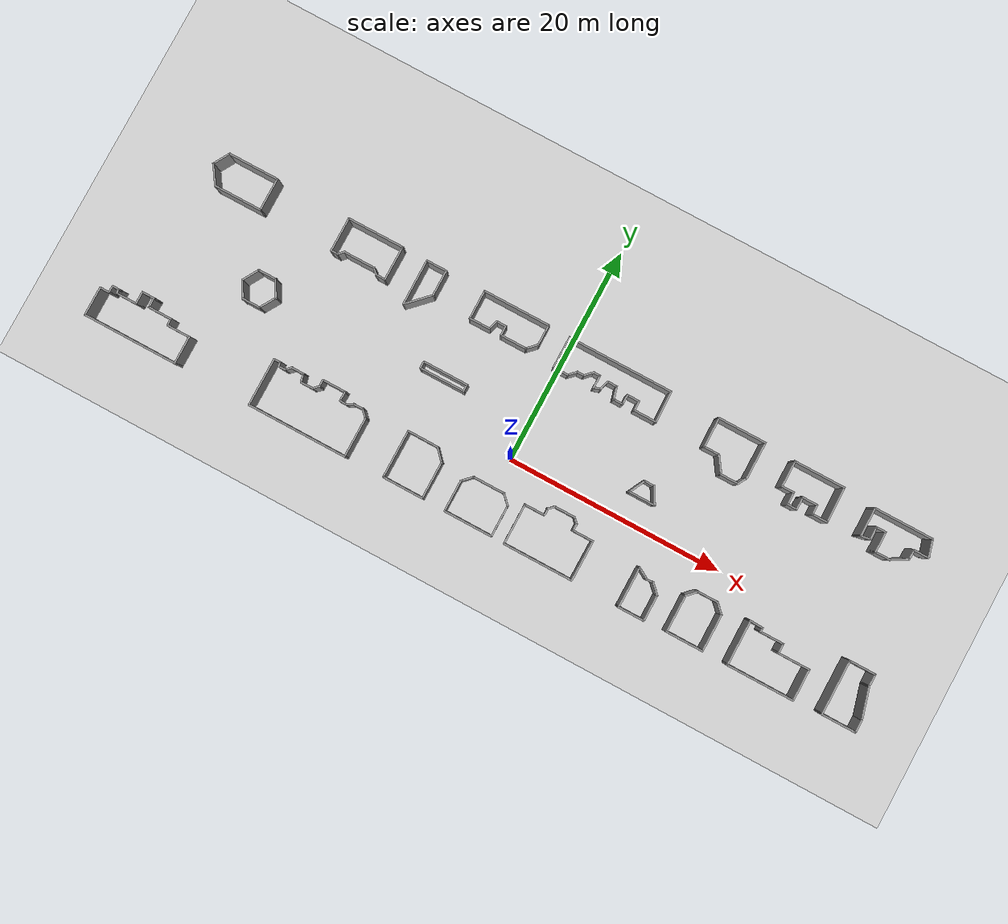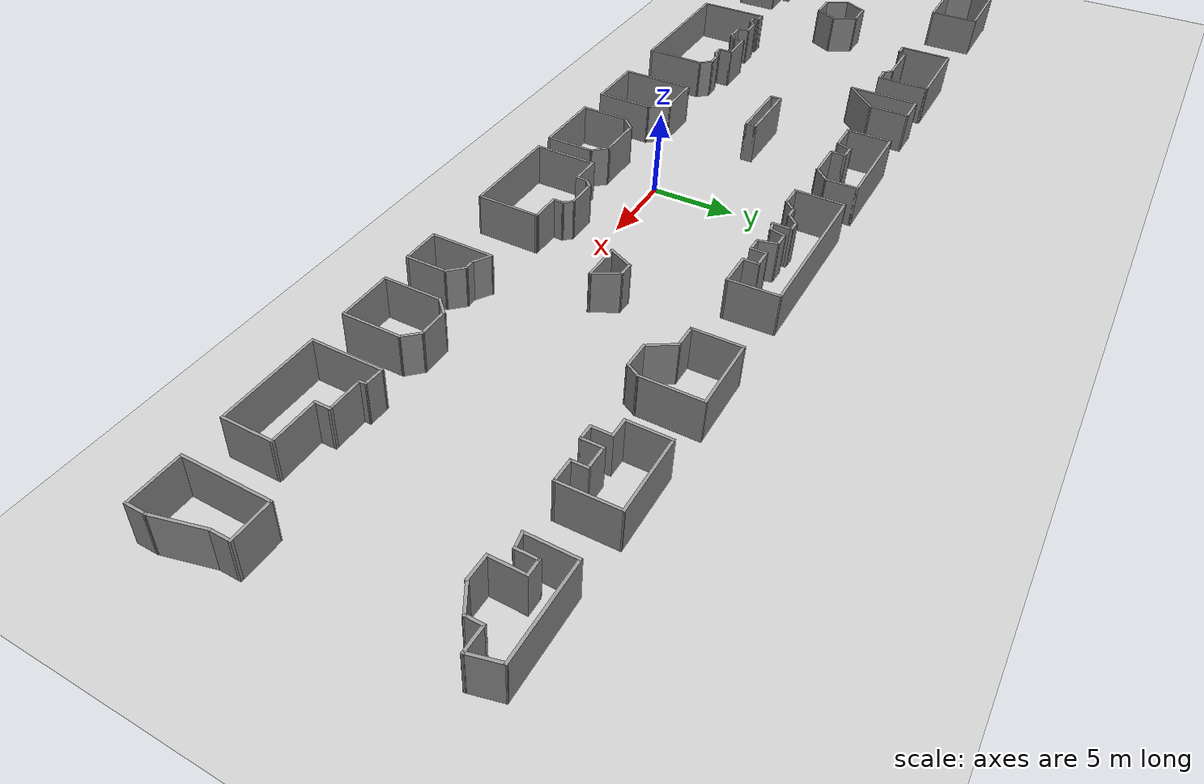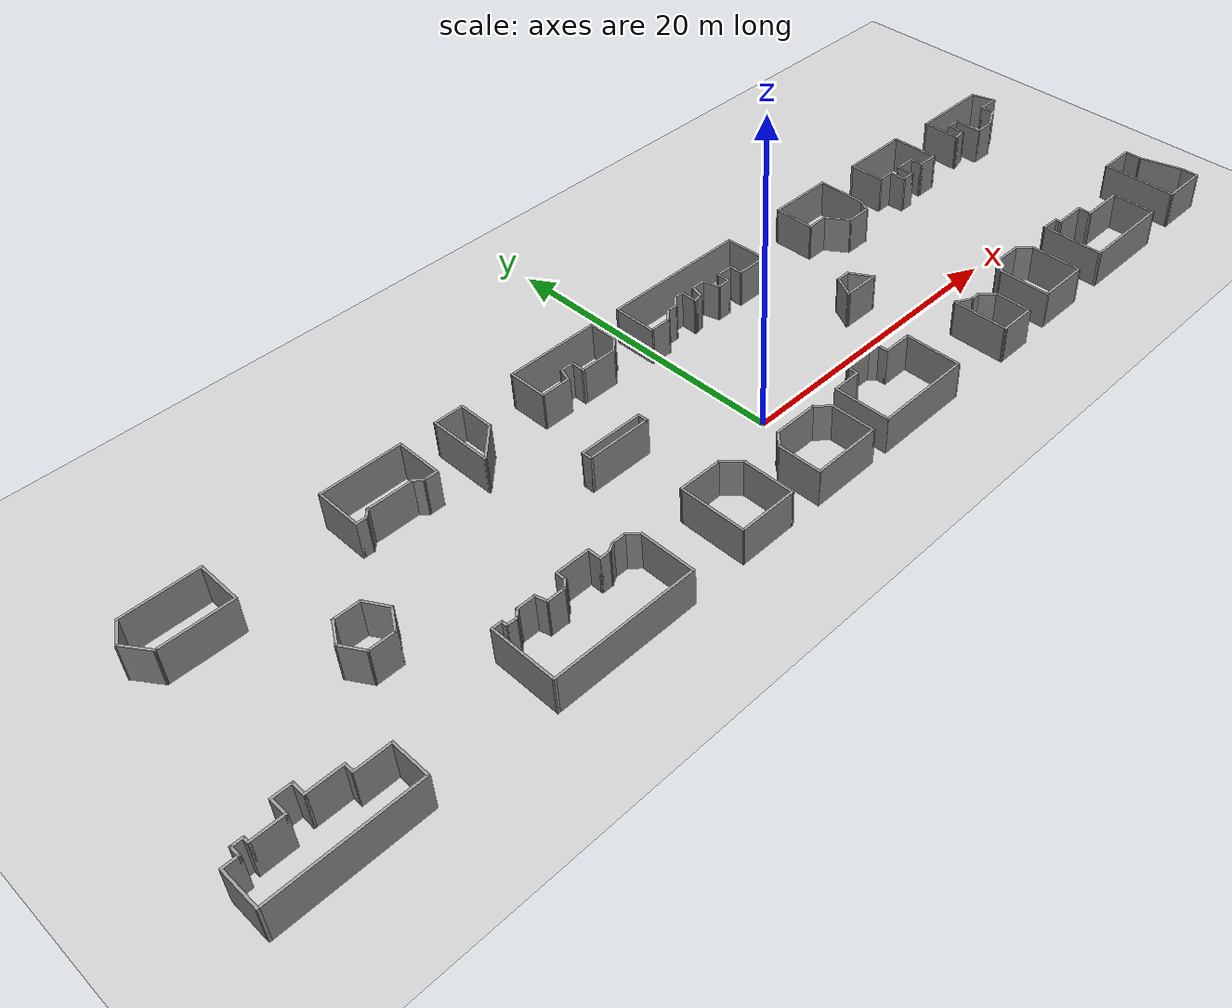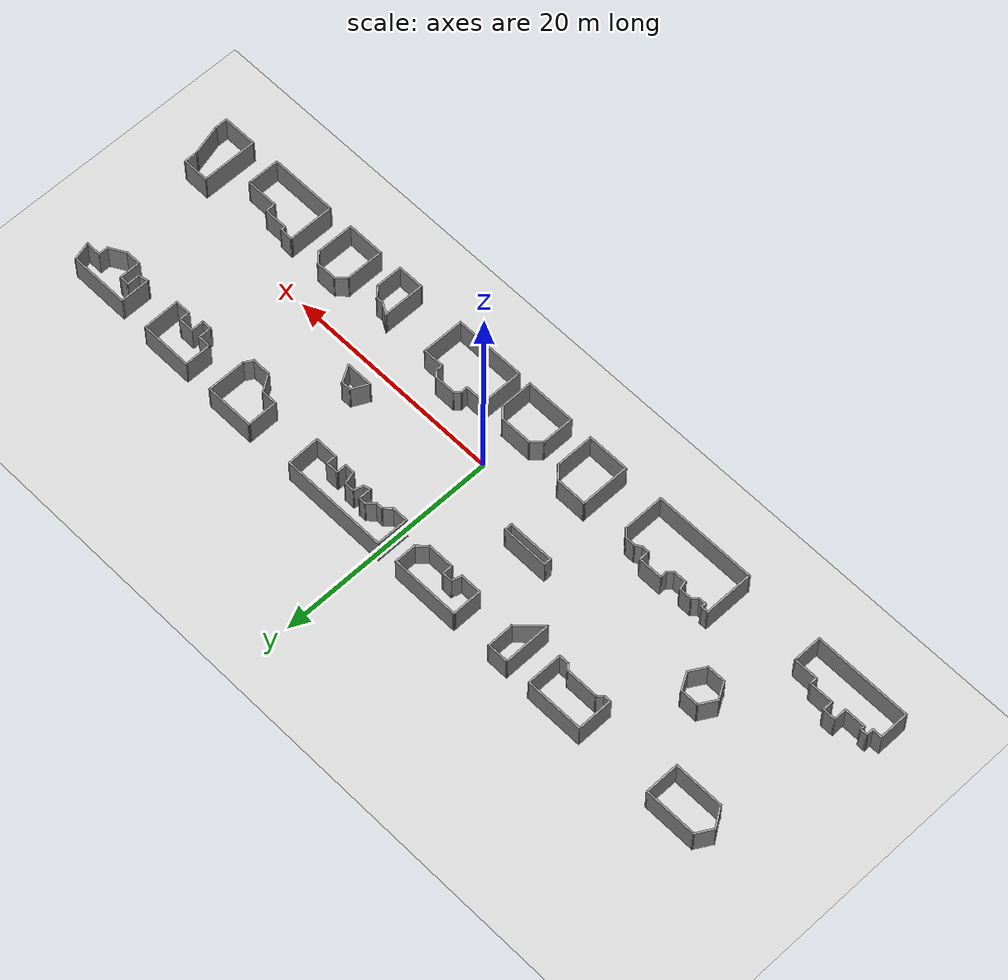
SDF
<sdf version="1.6">
 <world name="default">
  <light name="sun" type="directional">
   <pose>0 0 10 0 -0 0</pose>
   <diffuse>0.8 0.8 0.8 1</diffuse>
   <specular>0.1 0.1 0.1 1</specular>
   <attenuation>
    <range>1000</range>
    <constant>0.9</constant>
    <linear>0.01</linear>
    <quadratic>0.001</quadratic>
   </attenuation>
   <direction>-0.5 0.5 -1</direction>
  </light>
  <model name="ground_plane">
   <static>1</static>
   <link name="link">
    <collision name="collision">
     <geometry><plane><normal>0 0 1</normal><size>100 100</size></plane></geometry>
     <surface><friction><ode><mu>100</mu><mu2>50</mu2></ode></friction></surface>
    </collision>
    <visual name="visual">
     <cast_shadows>0</cast_shadows>
     <geometry><plane><normal>0 0 1</normal><size>100 100</size></plane></geometry>
     <material>
      <script><uri>file://media/materials/scripts/gazebo.material</uri><name>Gazebo/Grey</name></script>
     </material>
    </visual>
   </link>
  </model>
  <gravity>0 0 -9.8</gravity>
  <magnetic_field>6e-06 2.3e-05 -4.2e-05</magnetic_field>
  <atmosphere type="adiabatic"/>
  <physics name="default_physics" default="0" type="ode">
   <max_step_size>0.001</max_step_size>
   <real_time_factor>1</real_time_factor>
   <real_time_update_rate>1000</real_time_update_rate>
  </physics>
  <scene><ambient>0.4 0.4 0.4 1</ambient><background>0.7 0.7 0.7 1</background><shadows>1</shadows></scene>
  <spherical_coordinates>
   <surface_model>EARTH_WGS84</surface_model>
   <latitude_deg>0</latitude_deg>
   <longitude_deg>0</longitude_deg>
   <elevation>0</elevation>
   <heading_deg>0</heading_deg>
  </spherical_coordinates>
  <model name="corridor1">
   <pose>-0.71562 2.39478 0 0 -0 0</pose>
   <link name="Wall_102">
    <collision name="Wall_102_Collision">
     <geometry><box><size>1.25 0.15 2.5</size></box></geometry>
     <pose>0 0 1.25 0 -0 0</pose>
    </collision>
    <visual name="Wall_102_Visual">
     <pose>0 0 1.25 0 -0 0</pose>
     <geometry><box><size>1.25 0.15 2.5</size></box></geometry>
     <material>
      <script><uri>file://media/materials/scripts/gazebo.material</uri><name>Gazebo/Grey</name></script>
      <ambient>1 1 1 1</ambient>
     </material>
     <meta><layer>0</layer></meta>
    </visual>
    <pose>14.903 -5.59291 0 0 0 -0.523599</pose>
   </link>
   <link name="Wall_103">
    <collision name="Wall_103_Collision">
     <geometry><box><size>0.75 0.15 2.5</size></box></geometry>
     <pose>0 0 1.25 0 -0 0</pose>
    </collision>
    <visual name="Wall_103_Visual">
     <pose>0 0 1.25 0 -0 0</pose>
     <geometry><box><size>0.75 0.15 2.5</size></box></geometry>
     <material>
      <script><uri>file://media/materials/scripts/gazebo.material</uri><name>Gazebo/Grey</name></script>
      <ambient>1 1 1 1</ambient>
     </material>
     <meta><layer>0</layer></meta>
    </visual>
    <pose>15.6793 -5.86791 0 0 -0 0</pose>
   </link>
   <link name="Wall_104">
    <collision name="Wall_104_Collision">
     <geometry><box><size>1.25 0.15 2.5</size></box></geometry>
     <pose>0 0 1.25 0 -0 0</pose>
    </collision>
    <visual name="Wall_104_Visual">
     <pose>0 0 1.25 0 -0 0</pose>
     <geometry><box><size>1.25 0.15 2.5</size></box></geometry>
     <material>
      <script><uri>file://media/materials/scripts/gazebo.material</uri><name>Gazebo/Grey</name></script>
      <ambient>1 1 1 1</ambient>
     </material>
     <meta><layer>0</layer></meta>
    </visual>
    <pose>16.3682 -6.25681 0 0 0 -0.785398</pose>
   </link>
   <link name="Wall_105">
    <collision name="Wall_105_Collision">
     <geometry><box><size>2.5 0.15 2.5</size></box></geometry>
     <pose>0 0 1.25 0 -0 0</pose>
    </collision>
    <visual name="Wall_105_Visual">
     <pose>0 0 1.25 0 -0 0</pose>
     <geometry><box><size>2.5 0.15 2.5</size></box></geometry>
     <material>
      <script><uri>file://media/materials/scripts/gazebo.material</uri><name>Gazebo/Grey</name></script>
      <ambient>1 1 1 1</ambient>
     </material>
     <meta><layer>0</layer></meta>
    </visual>
    <pose>16.7571 -7.82072 0 0 0 -1.5708</pose>
   </link>
   <link name="Wall_106">
    <collision name="Wall_106_Collision">
     <geometry><box><size>2.5 0.15 2.5</size></box></geometry>
     <pose>0 0 1.25 0 -0 0</pose>
    </collision>
    <visual name="Wall_106_Visual">
     <pose>0 0 1.25 0 -0 0</pose>
     <geometry><box><size>2.5 0.15 2.5</size></box></geometry>
     <material>
      <script><uri>file://media/materials/scripts/gazebo.material</uri><name>Gazebo/Grey</name></script>
      <ambient>1 1 1 1</ambient>
     </material>
     <meta><layer>0</layer></meta>
    </visual>
    <pose>15.5821 -8.99572 0 0 -0 3.14159</pose>
   </link>
   <link name="Wall_107">
    <collision name="Wall_107_Collision">
     <geometry><box><size>3.82787 0.15 2.5</size></box></geometry>
     <pose>0 0 1.25 0 -0 0</pose>
    </collision>
    <visual name="Wall_107_Visual">
     <pose>0 0 1.25 0 -0 0</pose>
     <geometry><box><size>3.82787 0.15 2.5</size></box></geometry>
     <material>
      <script><uri>file://media/materials/scripts/gazebo.material</uri><name>Gazebo/Grey</name></script>
      <ambient>1 1 1 1</ambient>
     </material>
     <meta><layer>0</layer></meta>
    </visual>
    <pose>14.4169 -7.15681 0 0 -0 1.56548</pose>
   </link>
   <link name="Wall_109">
    <collision name="Wall_109_Collision">
     <geometry><box><size>1.25 0.15 2.5</size></box></geometry>
     <pose>0 0 1.25 0 -0 0</pose>
    </collision>
    <visual name="Wall_109_Visual">
     <pose>0 0 1.25 0 -0 0</pose>
     <geometry><box><size>1.25 0.15 2.5</size></box></geometry>
     <material>
      <script><uri>file://media/materials/scripts/gazebo.material</uri><name>Gazebo/Grey</name></script>
      <ambient>1 1 1 1</ambient>
     </material>
     <meta><layer>0</layer></meta>
    </visual>
    <pose>19.2123 -5.15015 0 0 0 -2.35619</pose>
   </link>
   <link name="Wall_110">
    <collision name="Wall_110_Collision">
     <geometry><box><size>3.5 0.15 2.5</size></box></geometry>
     <pose>0 0 1.25 0 -0 0</pose>
    </collision>
    <visual name="Wall_110_Visual">
     <pose>0 0 1.25 0 -0 0</pose>
     <geometry><box><size>3.5 0.15 2.5</size></box></geometry>
     <material>
      <script><uri>file://media/materials/scripts/gazebo.material</uri><name>Gazebo/Grey</name></script>
      <ambient>1 1 1 1</ambient>
     </material>
     <meta><layer>0</layer></meta>
    </visual>
    <pose>18.8234 -7.21406 0 0 0 -1.5708</pose>
   </link>
   <link name="Wall_111">
    <collision name="Wall_111_Collision">
     <geometry><box><size>3.5 0.15 2.5</size></box></geometry>
     <pose>0 0 1.25 0 -0 0</pose>
    </collision>
    <visual name="Wall_111_Visual">
     <pose>0 0 1.25 0 -0 0</pose>
     <geometry><box><size>3.5 0.15 2.5</size></box></geometry>
     <material>
      <script><uri>file://media/materials/scripts/gazebo.material</uri><name>Gazebo/Grey</name></script>
      <ambient>1 1 1 1</ambient>
     </material>
     <meta><layer>0</layer></meta>
    </visual>
    <pose>20.4984 -8.88906 0 0 -0 0</pose>
   </link>
   <link name="Wall_112">
    <collision name="Wall_112_Collision">
     <geometry><box><size>3.5 0.15 2.5</size></box></geometry>
     <pose>0 0 1.25 0 -0 0</pose>
    </collision>
    <visual name="Wall_112_Visual">
     <pose>0 0 1.25 0 -0 0</pose>
     <geometry><box><size>3.5 0.15 2.5</size></box></geometry>
     <material>
      <script><uri>file://media/materials/scripts/gazebo.material</uri><name>Gazebo/Grey</name></script>
      <ambient>1 1 1 1</ambient>
     </material>
     <meta><layer>0</layer></meta>
    </visual>
    <pose>22.1734 -7.21406 0 0 -0 1.5708</pose>
   </link>
   <link name="Wall_113">
    <collision name="Wall_113_Collision">
     <geometry><box><size>1.25 0.15 2.5</size></box></geometry>
     <pose>0 0 1.25 0 -0 0</pose>
    </collision>
    <visual name="Wall_113_Visual">
     <pose>0 0 1.25 0 -0 0</pose>
     <geometry><box><size>1.25 0.15 2.5</size></box></geometry>
     <material>
      <script><uri>file://media/materials/scripts/gazebo.material</uri><name>Gazebo/Grey</name></script>
      <ambient>1 1 1 1</ambient>
     </material>
     <meta><layer>0</layer></meta>
    </visual>
    <pose>21.7845 -5.15015 0 0 -0 2.35619</pose>
   </link>
   <link name="Wall_114">
    <collision name="Wall_114_Collision">
     <geometry><box><size>1.94436 0.15 2.5</size></box></geometry>
     <pose>0 0 1.25 0 -0 0</pose>
    </collision>
    <visual name="Wall_114_Visual">
     <pose>0 0 1.25 0 -0 0</pose>
     <geometry><box><size>1.94436 0.15 2.5</size></box></geometry>
     <material>
      <script><uri>file://media/materials/scripts/gazebo.material</uri><name>Gazebo/Grey</name></script>
      <ambient>1 1 1 1</ambient>
     </material>
     <meta><layer>0</layer></meta>
    </visual>
    <pose>20.4984 -4.76124 0 0 -0 3.14159</pose>
   </link>
   <link name="Wall_116">
    <collision name="Wall_116_Collision">
     <geometry><box><size>3.25 0.15 2.5</size></box></geometry>
     <pose>0 0 1.25 0 -0 0</pose>
    </collision>
    <visual name="Wall_116_Visual">
     <pose>0 0 1.25 0 -0 0</pose>
     <geometry><box><size>3.25 0.15 2.5</size></box></geometry>
     <material>
      <script><uri>file://media/materials/scripts/gazebo.material</uri><name>Gazebo/Grey</name></script>
      <ambient>1 1 1 1</ambient>
     </material>
     <meta><layer>0</layer></meta>
    </visual>
    <pose>-20.8032 7.35018 0 0 0 -1.5708</pose>
   </link>
   <link name="Wall_117">
    <collision name="Wall_117_Collision">
     <geometry><box><size>0.75 0.15 2.5</size></box></geometry>
     <pose>0 0 1.25 0 -0 0</pose>
    </collision>
    <visual name="Wall_117_Visual">
     <pose>0 0 1.25 0 -0 0</pose>
     <geometry><box><size>0.75 0.15 2.5</size></box></geometry>
     <material>
      <script><uri>file://media/materials/scripts/gazebo.material</uri><name>Gazebo/Grey</name></script>
      <ambient>1 1 1 1</ambient>
     </material>
     <meta><layer>0</layer></meta>
    </visual>
    <pose>-20.5032 5.80018 0 0 -0 0</pose>
   </link>
   <link name="Wall_118">
    <collision name="Wall_118_Collision">
     <geometry><box><size>0.75 0.15 2.5</size></box></geometry>
     <pose>0 0 1.25 0 -0 0</pose>
    </collision>
    <visual name="Wall_118_Visual">
     <pose>0 0 1.25 0 -0 0</pose>
     <geometry><box><size>0.75 0.15 2.5</size></box></geometry>
     <material>
      <script><uri>file://media/materials/scripts/gazebo.material</uri><name>Gazebo/Grey</name></script>
      <ambient>1 1 1 1</ambient>
     </material>
     <meta><layer>0</layer></meta>
    </visual>
    <pose>-19.991 6.01231 0 0 -0 0.785398</pose>
   </link>
   <link name="Wall_119">
    <collision name="Wall_119_Collision">
     <geometry><box><size>3 0.15 2.5</size></box></geometry>
     <pose>0 0 1.25 0 -0 0</pose>
    </collision>
    <visual name="Wall_119_Visual">
     <pose>0 0 1.25 0 -0 0</pose>
     <geometry><box><size>3 0.15 2.5</size></box></geometry>
     <material>
      <script><uri>file://media/materials/scripts/gazebo.material</uri><name>Gazebo/Grey</name></script>
      <ambient>1 1 1 1</ambient>
     </material>
     <meta><layer>0</layer></meta>
    </visual>
    <pose>-18.3539 6.22444 0 0 -0 0</pose>
   </link>
   <link name="Wall_120">
    <collision name="Wall_120_Collision">
     <geometry><box><size>0.75 0.15 2.5</size></box></geometry>
     <pose>0 0 1.25 0 -0 0</pose>
    </collision>
    <visual name="Wall_120_Visual">
     <pose>0 0 1.25 0 -0 0</pose>
     <geometry><box><size>0.75 0.15 2.5</size></box></geometry>
     <material>
      <script><uri>file://media/materials/scripts/gazebo.material</uri><name>Gazebo/Grey</name></script>
      <ambient>1 1 1 1</ambient>
     </material>
     <meta><layer>0</layer></meta>
    </visual>
    <pose>-16.7168 6.01231 0 0 0 -0.785398</pose>
   </link>
   <link name="Wall_123">
    <collision name="Wall_123_Collision">
     <geometry><box><size>1 0.15 2.5</size></box></geometry>
     <pose>0 0 1.25 0 -0 0</pose>
    </collision>
    <visual name="Wall_123_Visual">
     <pose>0 0 1.25 0 -0 0</pose>
     <geometry><box><size>1 0.15 2.5</size></box></geometry>
     <material>
      <script><uri>file://media/materials/scripts/gazebo.material</uri><name>Gazebo/Grey</name></script>
      <ambient>1 1 1 1</ambient>
     </material>
     <meta><layer>0</layer></meta>
    </visual>
    <pose>-16.0797 5.80018 0 0 -0 0</pose>
   </link>
   <link name="Wall_124">
    <collision name="Wall_124_Collision">
     <geometry><box><size>3.25 0.15 2.5</size></box></geometry>
     <pose>0 0 1.25 0 -0 0</pose>
    </collision>
    <visual name="Wall_124_Visual">
     <pose>0 0 1.25 0 -0 0</pose>
     <geometry><box><size>3.25 0.15 2.5</size></box></geometry>
     <material>
      <script><uri>file://media/materials/scripts/gazebo.material</uri><name>Gazebo/Grey</name></script>
      <ambient>1 1 1 1</ambient>
     </material>
     <meta><layer>0</layer></meta>
    </visual>
    <pose>-15.6547 7.35018 0 0 -0 1.5708</pose>
   </link>
   <link name="Wall_125">
    <collision name="Wall_125_Collision">
     <geometry><box><size>5.25 0.15 2.5</size></box></geometry>
     <pose>0 0 1.25 0 -0 0</pose>
    </collision>
    <visual name="Wall_125_Visual">
     <pose>0 0 1.25 0 -0 0</pose>
     <geometry><box><size>5.25 0.15 2.5</size></box></geometry>
     <material>
      <script><uri>file://media/materials/scripts/gazebo.material</uri><name>Gazebo/Grey</name></script>
      <ambient>1 1 1 1</ambient>
     </material>
     <meta><layer>0</layer></meta>
    </visual>
    <pose>-18.2047 8.90018 0 0 -0 3.14159</pose>
   </link>
   <link name="Wall_128">
    <collision name="Wall_128_Collision">
     <geometry><box><size>2 0.15 2.5</size></box></geometry>
     <pose>0 0 1.25 0 -0 0</pose>
    </collision>
    <visual name="Wall_128_Visual">
     <pose>0 0 1.25 0 -0 0</pose>
     <geometry><box><size>2 0.15 2.5</size></box></geometry>
     <material>
      <script><uri>file://media/materials/scripts/gazebo.material</uri><name>Gazebo/Grey</name></script>
      <ambient>1 1 1 1</ambient>
     </material>
     <meta><layer>0</layer></meta>
    </visual>
    <pose>-12.3978 8.8672 0 0 -0 3.14159</pose>
   </link>
   <link name="Wall_129">
    <collision name="Wall_129_Collision">
     <geometry><box><size>4.28996 0.15 2.5</size></box></geometry>
     <pose>0 0 1.25 0 -0 0</pose>
    </collision>
    <visual name="Wall_129_Visual">
     <pose>0 0 1.25 0 -0 0</pose>
     <geometry><box><size>4.28996 0.15 2.5</size></box></geometry>
     <material>
      <script><uri>file://media/materials/scripts/gazebo.material</uri><name>Gazebo/Grey</name></script>
      <ambient>1 1 1 1</ambient>
     </material>
     <meta><layer>0</layer></meta>
    </visual>
    <pose>-13.3129 6.79731 0 0 0 -1.56599</pose>
   </link>
   <link name="Wall_130">
    <collision name="Wall_130_Collision">
     <geometry><box><size>2.75 0.15 2.5</size></box></geometry>
     <pose>0 0 1.25 0 -0 0</pose>
    </collision>
    <visual name="Wall_130_Visual">
     <pose>0 0 1.25 0 -0 0</pose>
     <geometry><box><size>2.75 0.15 2.5</size></box></geometry>
     <material>
      <script><uri>file://media/materials/scripts/gazebo.material</uri><name>Gazebo/Grey</name></script>
      <ambient>1 1 1 1</ambient>
     </material>
     <meta><layer>0</layer></meta>
    </visual>
    <pose>-12.3638 5.64667 0 0 -0 0.785398</pose>
   </link>
   <link name="Wall_132">
    <collision name="Wall_132_Collision">
     <geometry><box><size>2.45147 0.15 2.5</size></box></geometry>
     <pose>0 0 1.25 0 -0 0</pose>
    </collision>
    <visual name="Wall_132_Visual">
     <pose>0 0 1.25 0 -0 0</pose>
     <geometry><box><size>2.45147 0.15 2.5</size></box></geometry>
     <material>
      <script><uri>file://media/materials/scripts/gazebo.material</uri><name>Gazebo/Grey</name></script>
      <ambient>1 1 1 1</ambient>
     </material>
     <meta><layer>0</layer></meta>
    </visual>
    <pose>-11.4687 7.71655 0 0 0 -1.56716</pose>
   </link>
   <link name="Wall_135">
    <collision name="Wall_135_Collision">
     <geometry><box><size>6.25 0.15 2.5</size></box></geometry>
     <pose>0 0 1.25 0 -0 0</pose>
    </collision>
    <visual name="Wall_135_Visual">
     <pose>0 0 1.25 0 -0 0</pose>
     <geometry><box><size>6.25 0.15 2.5</size></box></geometry>
     <material>
      <script><uri>file://media/materials/scripts/gazebo.material</uri><name>Gazebo/Grey</name></script>
      <ambient>1 1 1 1</ambient>
     </material>
     <meta><layer>0</layer></meta>
    </visual>
    <pose>-4.78429 8.90432 0 0 -0 0</pose>
   </link>
   <link name="Wall_138">
    <collision name="Wall_138_Collision">
     <geometry><box><size>2 0.15 2.5</size></box></geometry>
     <pose>0 0 1.25 0 -0 0</pose>
    </collision>
    <visual name="Wall_138_Visual">
     <pose>0 0 1.25 0 -0 0</pose>
     <geometry><box><size>2 0.15 2.5</size></box></geometry>
     <material>
      <script><uri>file://media/materials/scripts/gazebo.material</uri><name>Gazebo/Grey</name></script>
      <ambient>1 1 1 1</ambient>
     </material>
     <meta><layer>0</layer></meta>
    </visual>
    <pose>-1.73429 7.97931 0 0 0 -1.5708</pose>
   </link>
   <link name="Wall_139">
    <collision name="Wall_139_Collision">
     <geometry><box><size>1.25 0.15 2.5</size></box></geometry>
     <pose>0 0 1.25 0 -0 0</pose>
    </collision>
    <visual name="Wall_139_Visual">
     <pose>0 0 1.25 0 -0 0</pose>
     <geometry><box><size>1.25 0.15 2.5</size></box></geometry>
     <material>
      <script><uri>file://media/materials/scripts/gazebo.material</uri><name>Gazebo/Grey</name></script>
      <ambient>1 1 1 1</ambient>
     </material>
     <meta><layer>0</layer></meta>
    </visual>
    <pose>-2.1232 6.66541 0 0 0 -2.35619</pose>
   </link>
   <link name="Wall_140">
    <collision name="Wall_140_Collision">
     <geometry><box><size>2.5 0.15 2.5</size></box></geometry>
     <pose>0 0 1.25 0 -0 0</pose>
    </collision>
    <visual name="Wall_140_Visual">
     <pose>0 0 1.25 0 -0 0</pose>
     <geometry><box><size>2.5 0.15 2.5</size></box></geometry>
     <material>
      <script><uri>file://media/materials/scripts/gazebo.material</uri><name>Gazebo/Grey</name></script>
      <ambient>1 1 1 1</ambient>
     </material>
     <meta><layer>0</layer></meta>
    </visual>
    <pose>-3.68711 6.2765 0 0 -0 3.14159</pose>
   </link>
   <link name="Wall_141">
    <collision name="Wall_141_Collision">
     <geometry><box><size>1 0.15 2.5</size></box></geometry>
     <pose>0 0 1.25 0 -0 0</pose>
    </collision>
    <visual name="Wall_141_Visual">
     <pose>0 0 1.25 0 -0 0</pose>
     <geometry><box><size>1 0.15 2.5</size></box></geometry>
     <material>
      <script><uri>file://media/materials/scripts/gazebo.material</uri><name>Gazebo/Grey</name></script>
      <ambient>1 1 1 1</ambient>
     </material>
     <meta><layer>0</layer></meta>
    </visual>
    <pose>-4.86211 6.7015 0 0 -0 1.5708</pose>
   </link>
   <link name="Wall_142">
    <collision name="Wall_142_Collision">
     <geometry><box><size>1 0.15 2.5</size></box></geometry>
     <pose>0 0 1.25 0 -0 0</pose>
    </collision>
    <visual name="Wall_142_Visual">
     <pose>0 0 1.25 0 -0 0</pose>
     <geometry><box><size>1 0.15 2.5</size></box></geometry>
     <material>
      <script><uri>file://media/materials/scripts/gazebo.material</uri><name>Gazebo/Grey</name></script>
      <ambient>1 1 1 1</ambient>
     </material>
     <meta><layer>0</layer></meta>
    </visual>
    <pose>-5.28711 7.1265 0 0 -0 3.14159</pose>
   </link>
   <link name="Wall_143">
    <collision name="Wall_143_Collision">
     <geometry><box><size>0.989653 0.15 2.5</size></box></geometry>
     <pose>0 0 1.25 0 -0 0</pose>
    </collision>
    <visual name="Wall_143_Visual">
     <pose>0 0 1.25 0 -0 0</pose>
     <geometry><box><size>0.989653 0.15 2.5</size></box></geometry>
     <material>
      <script><uri>file://media/materials/scripts/gazebo.material</uri><name>Gazebo/Grey</name></script>
      <ambient>1 1 1 1</ambient>
     </material>
     <meta><layer>0</layer></meta>
    </visual>
    <pose>-5.84361 6.7278 0 0 0 -1.88939</pose>
   </link>
   <link name="Wall_144">
    <collision name="Wall_144_Collision">
     <geometry><box><size>2 0.15 2.5</size></box></geometry>
     <pose>0 0 1.25 0 -0 0</pose>
    </collision>
    <visual name="Wall_144_Visual">
     <pose>0 0 1.25 0 -0 0</pose>
     <geometry><box><size>2 0.15 2.5</size></box></geometry>
     <material>
      <script><uri>file://media/materials/scripts/gazebo.material</uri><name>Gazebo/Grey</name></script>
      <ambient>1 1 1 1</ambient>
     </material>
     <meta><layer>0</layer></meta>
    </visual>
    <pose>-6.90011 6.3028 0 0 -0 3.14159</pose>
   </link>
   <link name="Wall_146">
    <collision name="Wall_146_Collision">
     <geometry><box><size>2.75153 0.15 2.5</size></box></geometry>
     <pose>0 0 1.25 0 -0 0</pose>
    </collision>
    <visual name="Wall_146_Visual">
     <pose>0 0 1.25 0 -0 0</pose>
     <geometry><box><size>2.75153 0.15 2.5</size></box></geometry>
     <material>
      <script><uri>file://media/materials/scripts/gazebo.material</uri><name>Gazebo/Grey</name></script>
      <ambient>1 1 1 1</ambient>
     </material>
     <meta><layer>0</layer></meta>
    </visual>
    <pose>-7.8297 7.60356 0 0 0 -1.56727</pose>
   </link>
   <link name="Wall_148">
    <collision name="Wall_148_Collision">
     <geometry><box><size>3 0.15 2.5</size></box></geometry>
     <pose>0 0 1.25 0 -0 0</pose>
    </collision>
    <visual name="Wall_148_Visual">
     <pose>0 0 1.25 0 -0 0</pose>
     <geometry><box><size>3 0.15 2.5</size></box></geometry>
     <material>
      <script><uri>file://media/materials/scripts/gazebo.material</uri><name>Gazebo/Grey</name></script>
      <ambient>1 1 1 1</ambient>
     </material>
     <meta><layer>0</layer></meta>
    </visual>
    <pose>0.277223 7.41165 0 0 0 -1.5708</pose>
   </link>
   <link name="Wall_149">
    <collision name="Wall_149_Collision">
     <geometry><box><size>1.5 0.15 2.5</size></box></geometry>
     <pose>0 0 1.25 0 -0 0</pose>
    </collision>
    <visual name="Wall_149_Visual">
     <pose>0 0 1.25 0 -0 0</pose>
     <geometry><box><size>1.5 0.15 2.5</size></box></geometry>
     <material>
      <script><uri>file://media/materials/scripts/gazebo.material</uri><name>Gazebo/Grey</name></script>
      <ambient>1 1 1 1</ambient>
     </material>
     <meta><layer>0</layer></meta>
    </visual>
    <pose>0.952223 5.98665 0 0 -0 0</pose>
   </link>
   <link name="Wall_150">
    <collision name="Wall_150_Collision">
     <geometry><box><size>1 0.15 2.5</size></box></geometry>
     <pose>0 0 1.25 0 -0 0</pose>
    </collision>
    <visual name="Wall_150_Visual">
     <pose>0 0 1.25 0 -0 0</pose>
     <geometry><box><size>1 0.15 2.5</size></box></geometry>
     <material>
      <script><uri>file://media/materials/scripts/gazebo.material</uri><name>Gazebo/Grey</name></script>
      <ambient>1 1 1 1</ambient>
     </material>
     <meta><layer>0</layer></meta>
    </visual>
    <pose>1.92774 6.28718 0 0 -0 0.785398</pose>
   </link>
   <link name="Wall_151">
    <collision name="Wall_151_Collision">
     <geometry><box><size>0.75 0.15 2.5</size></box></geometry>
     <pose>0 0 1.25 0 -0 0</pose>
    </collision>
    <visual name="Wall_151_Visual">
     <pose>0 0 1.25 0 -0 0</pose>
     <geometry><box><size>0.75 0.15 2.5</size></box></geometry>
     <material>
      <script><uri>file://media/materials/scripts/gazebo.material</uri><name>Gazebo/Grey</name></script>
      <ambient>1 1 1 1</ambient>
     </material>
     <meta><layer>0</layer></meta>
    </visual>
    <pose>2.52826 6.5877 0 0 -0 0</pose>
   </link>
   <link name="Wall_152">
    <collision name="Wall_152_Collision">
     <geometry><box><size>1 0.15 2.5</size></box></geometry>
     <pose>0 0 1.25 0 -0 0</pose>
    </collision>
    <visual name="Wall_152_Visual">
     <pose>0 0 1.25 0 -0 0</pose>
     <geometry><box><size>1 0.15 2.5</size></box></geometry>
     <material>
      <script><uri>file://media/materials/scripts/gazebo.material</uri><name>Gazebo/Grey</name></script>
      <ambient>1 1 1 1</ambient>
     </material>
     <meta><layer>0</layer></meta>
    </visual>
    <pose>3.12878 6.88822 0 0 -0 0.785398</pose>
   </link>
   <link name="Wall_153">
    <collision name="Wall_153_Collision">
     <geometry><box><size>0.75 0.15 2.5</size></box></geometry>
     <pose>0 0 1.25 0 -0 0</pose>
    </collision>
    <visual name="Wall_153_Visual">
     <pose>0 0 1.25 0 -0 0</pose>
     <geometry><box><size>0.75 0.15 2.5</size></box></geometry>
     <material>
      <script><uri>file://media/materials/scripts/gazebo.material</uri><name>Gazebo/Grey</name></script>
      <ambient>1 1 1 1</ambient>
     </material>
     <meta><layer>0</layer></meta>
    </visual>
    <pose>3.72931 7.18874 0 0 -0 0</pose>
   </link>
   <link name="Wall_154">
    <collision name="Wall_154_Collision">
     <geometry><box><size>1.25 0.15 2.5</size></box></geometry>
     <pose>0 0 1.25 0 -0 0</pose>
    </collision>
    <visual name="Wall_154_Visual">
     <pose>0 0 1.25 0 -0 0</pose>
     <geometry><box><size>1.25 0.15 2.5</size></box></geometry>
     <material>
      <script><uri>file://media/materials/scripts/gazebo.material</uri><name>Gazebo/Grey</name></script>
      <ambient>1 1 1 1</ambient>
     </material>
     <meta><layer>0</layer></meta>
    </visual>
    <pose>4.0293 6.63874 0 0 0 -1.5708</pose>
   </link>
   <link name="Wall_155">
    <collision name="Wall_155_Collision">
     <geometry><box><size>0.75 0.15 2.5</size></box></geometry>
     <pose>0 0 1.25 0 -0 0</pose>
    </collision>
    <visual name="Wall_155_Visual">
     <pose>0 0 1.25 0 -0 0</pose>
     <geometry><box><size>0.75 0.15 2.5</size></box></geometry>
     <material>
      <script><uri>file://media/materials/scripts/gazebo.material</uri><name>Gazebo/Grey</name></script>
      <ambient>1 1 1 1</ambient>
     </material>
     <meta><layer>0</layer></meta>
    </visual>
    <pose>4.31908 6.16638 0 0 -0 0.261799</pose>
   </link>
   <link name="Wall_156">
    <collision name="Wall_156_Collision">
     <geometry><box><size>1 0.15 2.5</size></box></geometry>
     <pose>0 0 1.25 0 -0 0</pose>
    </collision>
    <visual name="Wall_156_Visual">
     <pose>0 0 1.25 0 -0 0</pose>
     <geometry><box><size>1 0.15 2.5</size></box></geometry>
     <material>
      <script><uri>file://media/materials/scripts/gazebo.material</uri><name>Gazebo/Grey</name></script>
      <ambient>1 1 1 1</ambient>
     </material>
     <meta><layer>0</layer></meta>
    </visual>
    <pose>4.71886 6.65454 0 0 -0 1.309</pose>
   </link>
   <link name="Wall_157">
    <collision name="Wall_157_Collision">
     <geometry><box><size>1 0.15 2.5</size></box></geometry>
     <pose>0 0 1.25 0 -0 0</pose>
    </collision>
    <visual name="Wall_157_Visual">
     <pose>0 0 1.25 0 -0 0</pose>
     <geometry><box><size>1 0.15 2.5</size></box></geometry>
     <material>
      <script><uri>file://media/materials/scripts/gazebo.material</uri><name>Gazebo/Grey</name></script>
      <ambient>1 1 1 1</ambient>
     </material>
     <meta><layer>0</layer></meta>
    </visual>
    <pose>5.25386 7.06506 0 0 -0 0</pose>
   </link>
   <link name="Wall_158">
    <collision name="Wall_158_Collision">
     <geometry><box><size>1.25 0.15 2.5</size></box></geometry>
     <pose>0 0 1.25 0 -0 0</pose>
    </collision>
    <visual name="Wall_158_Visual">
     <pose>0 0 1.25 0 -0 0</pose>
     <geometry><box><size>1.25 0.15 2.5</size></box></geometry>
     <material>
      <script><uri>file://media/materials/scripts/gazebo.material</uri><name>Gazebo/Grey</name></script>
      <ambient>1 1 1 1</ambient>
     </material>
     <meta><layer>0</layer></meta>
    </visual>
    <pose>5.82121 6.53381 0 0 0 -1.309</pose>
   </link>
   <link name="Wall_159">
    <collision name="Wall_159_Collision">
     <geometry><box><size>1 0.15 2.5</size></box></geometry>
     <pose>0 0 1.25 0 -0 0</pose>
    </collision>
    <visual name="Wall_159_Visual">
     <pose>0 0 1.25 0 -0 0</pose>
     <geometry><box><size>1 0.15 2.5</size></box></geometry>
     <material>
      <script><uri>file://media/materials/scripts/gazebo.material</uri><name>Gazebo/Grey</name></script>
      <ambient>1 1 1 1</ambient>
     </material>
     <meta><layer>0</layer></meta>
    </visual>
    <pose>6.38856 6.00255 0 0 -0 0</pose>
   </link>
   <link name="Wall_160">
    <collision name="Wall_160_Collision">
     <geometry><box><size>1 0.15 2.5</size></box></geometry>
     <pose>0 0 1.25 0 -0 0</pose>
    </collision>
    <visual name="Wall_160_Visual">
     <pose>0 0 1.25 0 -0 0</pose>
     <geometry><box><size>1 0.15 2.5</size></box></geometry>
     <material>
      <script><uri>file://media/materials/scripts/gazebo.material</uri><name>Gazebo/Grey</name></script>
      <ambient>1 1 1 1</ambient>
     </material>
     <meta><layer>0</layer></meta>
    </visual>
    <pose>6.81356 6.42755 0 0 -0 1.5708</pose>
   </link>
   <link name="Wall_161">
    <collision name="Wall_161_Collision">
     <geometry><box><size>1.25 0.15 2.5</size></box></geometry>
     <pose>0 0 1.25 0 -0 0</pose>
    </collision>
    <visual name="Wall_161_Visual">
     <pose>0 0 1.25 0 -0 0</pose>
     <geometry><box><size>1.25 0.15 2.5</size></box></geometry>
     <material>
      <script><uri>file://media/materials/scripts/gazebo.material</uri><name>Gazebo/Grey</name></script>
      <ambient>1 1 1 1</ambient>
     </material>
     <meta><layer>0</layer></meta>
    </visual>
    <pose>7.36356 6.85255 0 0 -0 0</pose>
   </link>
   <link name="Wall_162">
    <collision name="Wall_162_Collision">
     <geometry><box><size>1 0.15 2.5</size></box></geometry>
     <pose>0 0 1.25 0 -0 0</pose>
    </collision>
    <visual name="Wall_162_Visual">
     <pose>0 0 1.25 0 -0 0</pose>
     <geometry><box><size>1 0.15 2.5</size></box></geometry>
     <material>
      <script><uri>file://media/materials/scripts/gazebo.material</uri><name>Gazebo/Grey</name></script>
      <ambient>1 1 1 1</ambient>
     </material>
     <meta><layer>0</layer></meta>
    </visual>
    <pose>7.91356 6.42755 0 0 0 -1.5708</pose>
   </link>
   <link name="Wall_167">
    <collision name="Wall_167_Collision">
     <geometry><box><size>9.75 0.15 2.5</size></box></geometry>
     <pose>0 0 1.25 0 -0 0</pose>
    </collision>
    <visual name="Wall_167_Visual">
     <pose>0 0 1.25 0 -0 0</pose>
     <geometry><box><size>9.75 0.15 2.5</size></box></geometry>
     <material>
      <script><uri>file://media/materials/scripts/gazebo.material</uri><name>Gazebo/Grey</name></script>
      <ambient>1 1 1 1</ambient>
     </material>
     <meta><layer>0</layer></meta>
    </visual>
    <pose>5.07722 8.83665 0 0 -0 0</pose>
   </link>
   <link name="Wall_169">
    <collision name="Wall_169_Collision">
     <geometry><box><size>2.18935 0.15 2.5</size></box></geometry>
     <pose>0 0 1.25 0 -0 0</pose>
    </collision>
    <visual name="Wall_169_Visual">
     <pose>0 0 1.25 0 -0 0</pose>
     <geometry><box><size>2.18935 0.15 2.5</size></box></geometry>
     <material>
      <script><uri>file://media/materials/scripts/gazebo.material</uri><name>Gazebo/Grey</name></script>
      <ambient>1 1 1 1</ambient>
     </material>
     <meta><layer>0</layer></meta>
    </visual>
    <pose>8.93323 6.00105 0 0 0 -0.001463</pose>
   </link>
   <link name="Wall_176">
    <collision name="Wall_176_Collision">
     <geometry><box><size>2.9881 0.15 2.5</size></box></geometry>
     <pose>0 0 1.25 0 -0 0</pose>
    </collision>
    <visual name="Wall_176_Visual">
     <pose>0 0 1.25 0 -0 0</pose>
     <geometry><box><size>2.9881 0.15 2.5</size></box></geometry>
     <material>
      <script><uri>file://media/materials/scripts/gazebo.material</uri><name>Gazebo/Grey</name></script>
      <ambient>1 1 1 1</ambient>
     </material>
     <meta><layer>0</layer></meta>
    </visual>
    <pose>9.91506 7.41811 0 0 -0 1.59746</pose>
   </link>
   <link name="Wall_179">
    <collision name="Wall_179_Collision">
     <geometry><box><size>4.5 0.15 2.5</size></box></geometry>
     <pose>0 0 1.25 0 -0 0</pose>
    </collision>
    <visual name="Wall_179_Visual">
     <pose>0 0 1.25 0 -0 0</pose>
     <geometry><box><size>4.5 0.15 2.5</size></box></geometry>
     <material>
      <script><uri>file://media/materials/scripts/gazebo.material</uri><name>Gazebo/Grey</name></script>
      <ambient>1 1 1 1</ambient>
     </material>
     <meta><layer>0</layer></meta>
    </visual>
    <pose>16.6017 8.78209 0 0 -0 0</pose>
   </link>
   <link name="Wall_180">
    <collision name="Wall_180_Collision">
     <geometry><box><size>3.5 0.15 2.5</size></box></geometry>
     <pose>0 0 1.25 0 -0 0</pose>
    </collision>
    <visual name="Wall_180_Visual">
     <pose>0 0 1.25 0 -0 0</pose>
     <geometry><box><size>3.5 0.15 2.5</size></box></geometry>
     <material>
      <script><uri>file://media/materials/scripts/gazebo.material</uri><name>Gazebo/Grey</name></script>
      <ambient>1 1 1 1</ambient>
     </material>
     <meta><layer>0</layer></meta>
    </visual>
    <pose>18.7767 7.1071 0 0 0 -1.5708</pose>
   </link>
   <link name="Wall_181">
    <collision name="Wall_181_Collision">
     <geometry><box><size>1 0.15 2.5</size></box></geometry>
     <pose>0 0 1.25 0 -0 0</pose>
    </collision>
    <visual name="Wall_181_Visual">
     <pose>0 0 1.25 0 -0 0</pose>
     <geometry><box><size>1 0.15 2.5</size></box></geometry>
     <material>
      <script><uri>file://media/materials/scripts/gazebo.material</uri><name>Gazebo/Grey</name></script>
      <ambient>1 1 1 1</ambient>
     </material>
     <meta><layer>0</layer></meta>
    </visual>
    <pose>18.5642 5.06403 0 0 0 -2.0944</pose>
   </link>
   <link name="Wall_182">
    <collision name="Wall_182_Collision">
     <geometry><box><size>1.75 0.15 2.5</size></box></geometry>
     <pose>0 0 1.25 0 -0 0</pose>
    </collision>
    <visual name="Wall_182_Visual">
     <pose>0 0 1.25 0 -0 0</pose>
     <geometry><box><size>1.75 0.15 2.5</size></box></geometry>
     <material>
      <script><uri>file://media/materials/scripts/gazebo.material</uri><name>Gazebo/Grey</name></script>
      <ambient>1 1 1 1</ambient>
     </material>
     <meta><layer>0</layer></meta>
    </visual>
    <pose>17.5517 4.69597 0 0 -0 3.14159</pose>
   </link>
   <link name="Wall_183">
    <collision name="Wall_183_Collision">
     <geometry><box><size>1.82178 0.15 2.5</size></box></geometry>
     <pose>0 0 1.25 0 -0 0</pose>
    </collision>
    <visual name="Wall_183_Visual">
     <pose>0 0 1.25 0 -0 0</pose>
     <geometry><box><size>1.82178 0.15 2.5</size></box></geometry>
     <material>
      <script><uri>file://media/materials/scripts/gazebo.material</uri><name>Gazebo/Grey</name></script>
      <ambient>1 1 1 1</ambient>
     </material>
     <meta><layer>0</layer></meta>
    </visual>
    <pose>16.284 5.38879 0 0 -0 2.16456</pose>
   </link>
   <link name="Wall_184">
    <collision name="Wall_184_Collision">
     <geometry><box><size>1.5 0.15 2.5</size></box></geometry>
     <pose>0 0 1.25 0 -0 0</pose>
    </collision>
    <visual name="Wall_184_Visual">
     <pose>0 0 1.25 0 -0 0</pose>
     <geometry><box><size>1.5 0.15 2.5</size></box></geometry>
     <material>
      <script><uri>file://media/materials/scripts/gazebo.material</uri><name>Gazebo/Grey</name></script>
      <ambient>1 1 1 1</ambient>
     </material>
     <meta><layer>0</layer></meta>
    </visual>
    <pose>15.1263 6.08161 0 0 -0 3.14159</pose>
   </link>
   <link name="Wall_186">
    <collision name="Wall_186_Collision">
     <geometry><box><size>2.85059 0.15 2.5</size></box></geometry>
     <pose>0 0 1.25 0 -0 0</pose>
    </collision>
    <visual name="Wall_186_Visual">
     <pose>0 0 1.25 0 -0 0</pose>
     <geometry><box><size>2.85059 0.15 2.5</size></box></geometry>
     <material>
      <script><uri>file://media/materials/scripts/gazebo.material</uri><name>Gazebo/Grey</name></script>
      <ambient>1 1 1 1</ambient>
     </material>
     <meta><layer>0</layer></meta>
    </visual>
    <pose>14.439 7.43185 0 0 0 -1.56168</pose>
   </link>
   <link name="Wall_188">
    <collision name="Wall_188_Collision">
     <geometry><box><size>2.5 0.15 2.5</size></box></geometry>
     <pose>0 0 1.25 0 -0 0</pose>
    </collision>
    <visual name="Wall_188_Visual">
     <pose>0 0 1.25 0 -0 0</pose>
     <geometry><box><size>2.5 0.15 2.5</size></box></geometry>
     <material>
      <script><uri>file://media/materials/scripts/gazebo.material</uri><name>Gazebo/Grey</name></script>
      <ambient>1 1 1 1</ambient>
     </material>
     <meta><layer>0</layer></meta>
    </visual>
    <pose>21.6645 7.41156 0 0 0 -1.5708</pose>
   </link>
   <link name="Wall_189">
    <collision name="Wall_189_Collision">
     <geometry><box><size>1.25 0.15 2.5</size></box></geometry>
     <pose>0 0 1.25 0 -0 0</pose>
    </collision>
    <visual name="Wall_189_Visual">
     <pose>0 0 1.25 0 -0 0</pose>
     <geometry><box><size>1.25 0.15 2.5</size></box></geometry>
     <material>
      <script><uri>file://media/materials/scripts/gazebo.material</uri><name>Gazebo/Grey</name></script>
      <ambient>1 1 1 1</ambient>
     </material>
     <meta><layer>0</layer></meta>
    </visual>
    <pose>22.2145 6.23656 0 0 -0 0</pose>
   </link>
   <link name="Wall_190">
    <collision name="Wall_190_Collision">
     <geometry><box><size>1.25 0.15 2.5</size></box></geometry>
     <pose>0 0 1.25 0 -0 0</pose>
    </collision>
    <visual name="Wall_190_Visual">
     <pose>0 0 1.25 0 -0 0</pose>
     <geometry><box><size>1.25 0.15 2.5</size></box></geometry>
     <material>
      <script><uri>file://media/materials/scripts/gazebo.material</uri><name>Gazebo/Grey</name></script>
      <ambient>1 1 1 1</ambient>
     </material>
     <meta><layer>0</layer></meta>
    </visual>
    <pose>22.7645 5.68656 0 0 0 -1.5708</pose>
   </link>
   <link name="Wall_191">
    <collision name="Wall_191_Collision">
     <geometry><box><size>1 0.15 2.5</size></box></geometry>
     <pose>0 0 1.25 0 -0 0</pose>
    </collision>
    <visual name="Wall_191_Visual">
     <pose>0 0 1.25 0 -0 0</pose>
     <geometry><box><size>1 0.15 2.5</size></box></geometry>
     <material>
      <script><uri>file://media/materials/scripts/gazebo.material</uri><name>Gazebo/Grey</name></script>
      <ambient>1 1 1 1</ambient>
     </material>
     <meta><layer>0</layer></meta>
    </visual>
    <pose>23.1895 5.13656 0 0 -0 0</pose>
   </link>
   <link name="Wall_192">
    <collision name="Wall_192_Collision">
     <geometry><box><size>1.25 0.15 2.5</size></box></geometry>
     <pose>0 0 1.25 0 -0 0</pose>
    </collision>
    <visual name="Wall_192_Visual">
     <pose>0 0 1.25 0 -0 0</pose>
     <geometry><box><size>1.25 0.15 2.5</size></box></geometry>
     <material>
      <script><uri>file://media/materials/scripts/gazebo.material</uri><name>Gazebo/Grey</name></script>
      <ambient>1 1 1 1</ambient>
     </material>
     <meta><layer>0</layer></meta>
    </visual>
    <pose>23.6145 5.68656 0 0 -0 1.5708</pose>
   </link>
   <link name="Wall_193">
    <collision name="Wall_193_Collision">
     <geometry><box><size>1.5 0.15 2.5</size></box></geometry>
     <pose>0 0 1.25 0 -0 0</pose>
    </collision>
    <visual name="Wall_193_Visual">
     <pose>0 0 1.25 0 -0 0</pose>
     <geometry><box><size>1.5 0.15 2.5</size></box></geometry>
     <material>
      <script><uri>file://media/materials/scripts/gazebo.material</uri><name>Gazebo/Grey</name></script>
      <ambient>1 1 1 1</ambient>
     </material>
     <meta><layer>0</layer></meta>
    </visual>
    <pose>24.2895 6.23656 0 0 -0 0</pose>
   </link>
   <link name="Wall_194">
    <collision name="Wall_194_Collision">
     <geometry><box><size>1 0.15 2.5</size></box></geometry>
     <pose>0 0 1.25 0 -0 0</pose>
    </collision>
    <visual name="Wall_194_Visual">
     <pose>0 0 1.25 0 -0 0</pose>
     <geometry><box><size>1 0.15 2.5</size></box></geometry>
     <material>
      <script><uri>file://media/materials/scripts/gazebo.material</uri><name>Gazebo/Grey</name></script>
      <ambient>1 1 1 1</ambient>
     </material>
     <meta><layer>0</layer></meta>
    </visual>
    <pose>24.9645 5.81156 0 0 0 -1.5708</pose>
   </link>
   <link name="Wall_197">
    <collision name="Wall_197_Collision">
     <geometry><box><size>1.5 0.15 2.5</size></box></geometry>
     <pose>0 0 1.25 0 -0 0</pose>
    </collision>
    <visual name="Wall_197_Visual">
     <pose>0 0 1.25 0 -0 0</pose>
     <geometry><box><size>1.5 0.15 2.5</size></box></geometry>
     <material>
      <script><uri>file://media/materials/scripts/gazebo.material</uri><name>Gazebo/Grey</name></script>
      <ambient>1 1 1 1</ambient>
     </material>
     <meta><layer>0</layer></meta>
    </visual>
    <pose>25.6395 5.38656 0 0 -0 0</pose>
   </link>
   <link name="Wall_198">
    <collision name="Wall_198_Collision">
     <geometry><box><size>3.35039 0.15 2.5</size></box></geometry>
     <pose>0 0 1.25 0 -0 0</pose>
    </collision>
    <visual name="Wall_198_Visual">
     <pose>0 0 1.25 0 -0 0</pose>
     <geometry><box><size>3.35039 0.15 2.5</size></box></geometry>
     <material>
      <script><uri>file://media/materials/scripts/gazebo.material</uri><name>Gazebo/Grey</name></script>
      <ambient>1 1 1 1</ambient>
     </material>
     <meta><layer>0</layer></meta>
    </visual>
    <pose>26.2895 6.98656 0 0 -0 1.58642</pose>
   </link>
   <link name="Wall_199">
    <collision name="Wall_199_Collision">
     <geometry><box><size>4.75 0.15 2.5</size></box></geometry>
     <pose>0 0 1.25 0 -0 0</pose>
    </collision>
    <visual name="Wall_199_Visual">
     <pose>0 0 1.25 0 -0 0</pose>
     <geometry><box><size>4.75 0.15 2.5</size></box></geometry>
     <material>
      <script><uri>file://media/materials/scripts/gazebo.material</uri><name>Gazebo/Grey</name></script>
      <ambient>1 1 1 1</ambient>
     </material>
     <meta><layer>0</layer></meta>
    </visual>
    <pose>23.9645 8.58656 0 0 -0 3.14159</pose>
   </link>
   <link name="Wall_202">
    <collision name="Wall_202_Collision">
     <geometry><box><size>2.05612 0.15 2.5</size></box></geometry>
     <pose>0 0 1.25 0 -0 0</pose>
    </collision>
    <visual name="Wall_202_Visual">
     <pose>0 0 1.25 0 -0 0</pose>
     <geometry><box><size>2.05612 0.15 2.5</size></box></geometry>
     <material>
      <script><uri>file://media/materials/scripts/gazebo.material</uri><name>Gazebo/Grey</name></script>
      <ambient>1 1 1 1</ambient>
     </material>
     <meta><layer>0</layer></meta>
    </visual>
    <pose>-32.5914 6.7906 0 0 -0 2.15987</pose>
   </link>
   <link name="Wall_203">
    <collision name="Wall_203_Collision">
     <geometry><box><size>1.75 0.15 2.5</size></box></geometry>
     <pose>0 0 1.25 0 -0 0</pose>
    </collision>
    <visual name="Wall_203_Visual">
     <pose>0 0 1.25 0 -0 0</pose>
     <geometry><box><size>1.75 0.15 2.5</size></box></geometry>
     <material>
      <script><uri>file://media/materials/scripts/gazebo.material</uri><name>Gazebo/Grey</name></script>
      <ambient>1 1 1 1</ambient>
     </material>
     <meta><layer>0</layer></meta>
    </visual>
    <pose>-32.7209 8.27585 0 0 -0 1.0472</pose>
   </link>
   <link name="Wall_204">
    <collision name="Wall_204_Collision">
     <geometry><box><size>4.75 0.15 2.5</size></box></geometry>
     <pose>0 0 1.25 0 -0 0</pose>
    </collision>
    <visual name="Wall_204_Visual">
     <pose>0 0 1.25 0 -0 0</pose>
     <geometry><box><size>4.75 0.15 2.5</size></box></geometry>
     <material>
      <script><uri>file://media/materials/scripts/gazebo.material</uri><name>Gazebo/Grey</name></script>
      <ambient>1 1 1 1</ambient>
     </material>
     <meta><layer>0</layer></meta>
    </visual>
    <pose>-30.0209 8.96867 0 0 -0 0</pose>
   </link>
   <link name="Wall_205">
    <collision name="Wall_205_Collision">
     <geometry><box><size>3 0.15 2.5</size></box></geometry>
     <pose>0 0 1.25 0 -0 0</pose>
    </collision>
    <visual name="Wall_205_Visual">
     <pose>0 0 1.25 0 -0 0</pose>
     <geometry><box><size>3 0.15 2.5</size></box></geometry>
     <material>
      <script><uri>file://media/materials/scripts/gazebo.material</uri><name>Gazebo/Grey</name></script>
      <ambient>1 1 1 1</ambient>
     </material>
     <meta><layer>0</layer></meta>
    </visual>
    <pose>-27.7209 7.54367 0 0 0 -1.5708</pose>
   </link>
   <link name="Wall_207">
    <collision name="Wall_207_Collision">
     <geometry><box><size>4.5 0.15 2.5</size></box></geometry>
     <pose>0 0 1.25 0 -0 0</pose>
    </collision>
    <visual name="Wall_207_Visual">
     <pose>0 0 1.25 0 -0 0</pose>
     <geometry><box><size>4.5 0.15 2.5</size></box></geometry>
     <material>
      <script><uri>file://media/materials/scripts/gazebo.material</uri><name>Gazebo/Grey</name></script>
      <ambient>1 1 1 1</ambient>
     </material>
     <meta><layer>0</layer></meta>
    </visual>
    <pose>-29.9042 5.99817 0 0 -0 0</pose>
   </link>
   <link name="Wall_212">
    <collision name="Wall_212_Collision">
     <geometry><box><size>8.75 0.15 2.5</size></box></geometry>
     <pose>0 0 1.25 0 -0 0</pose>
    </collision>
    <visual name="Wall_212_Visual">
     <pose>0 0 1.25 0 -0 0</pose>
     <geometry><box><size>8.75 0.15 2.5</size></box></geometry>
     <material>
      <script><uri>file://media/materials/scripts/gazebo.material</uri><name>Gazebo/Grey</name></script>
      <ambient>1 1 1 1</ambient>
     </material>
     <meta><layer>0</layer></meta>
    </visual>
    <pose>-32.0209 -8.73133 0 0 -0 3.14159</pose>
   </link>
   <link name="Wall_213">
    <collision name="Wall_213_Collision">
     <geometry><box><size>2.75 0.15 2.5</size></box></geometry>
     <pose>0 0 1.25 0 -0 0</pose>
    </collision>
    <visual name="Wall_213_Visual">
     <pose>0 0 1.25 0 -0 0</pose>
     <geometry><box><size>2.75 0.15 2.5</size></box></geometry>
     <material>
      <script><uri>file://media/materials/scripts/gazebo.material</uri><name>Gazebo/Grey</name></script>
      <ambient>1 1 1 1</ambient>
     </material>
     <meta><layer>0</layer></meta>
    </visual>
    <pose>-36.3209 -7.43133 0 0 -0 1.5708</pose>
   </link>
   <link name="Wall_214">
    <collision name="Wall_214_Collision">
     <geometry><box><size>1 0.15 2.5</size></box></geometry>
     <pose>0 0 1.25 0 -0 0</pose>
    </collision>
    <visual name="Wall_214_Visual">
     <pose>0 0 1.25 0 -0 0</pose>
     <geometry><box><size>1 0.15 2.5</size></box></geometry>
     <material>
      <script><uri>file://media/materials/scripts/gazebo.material</uri><name>Gazebo/Grey</name></script>
      <ambient>1 1 1 1</ambient>
     </material>
     <meta><layer>0</layer></meta>
    </visual>
    <pose>-35.8959 -6.13133 0 0 -0 0</pose>
   </link>
   <link name="Wall_215">
    <collision name="Wall_215_Collision">
     <geometry><box><size>0.75 0.15 2.5</size></box></geometry>
     <pose>0 0 1.25 0 -0 0</pose>
    </collision>
    <visual name="Wall_215_Visual">
     <pose>0 0 1.25 0 -0 0</pose>
     <geometry><box><size>0.75 0.15 2.5</size></box></geometry>
     <material>
      <script><uri>file://media/materials/scripts/gazebo.material</uri><name>Gazebo/Grey</name></script>
      <ambient>1 1 1 1</ambient>
     </material>
     <meta><layer>0</layer></meta>
    </visual>
    <pose>-35.4709 -5.83133 0 0 -0 1.5708</pose>
   </link>
   <link name="Wall_216">
    <collision name="Wall_216_Collision">
     <geometry><box><size>0.75 0.15 2.5</size></box></geometry>
     <pose>0 0 1.25 0 -0 0</pose>
    </collision>
    <visual name="Wall_216_Visual">
     <pose>0 0 1.25 0 -0 0</pose>
     <geometry><box><size>0.75 0.15 2.5</size></box></geometry>
     <material>
      <script><uri>file://media/materials/scripts/gazebo.material</uri><name>Gazebo/Grey</name></script>
      <ambient>1 1 1 1</ambient>
     </material>
     <meta><layer>0</layer></meta>
    </visual>
    <pose>-35.1709 -5.53133 0 0 -0 0</pose>
   </link>
   <link name="Wall_217">
    <collision name="Wall_217_Collision">
     <geometry><box><size>0.5 0.15 2.5</size></box></geometry>
     <pose>0 0 1.25 0 -0 0</pose>
    </collision>
    <visual name="Wall_217_Visual">
     <pose>0 0 1.25 0 -0 0</pose>
     <geometry><box><size>0.5 0.15 2.5</size></box></geometry>
     <material>
      <script><uri>file://media/materials/scripts/gazebo.material</uri><name>Gazebo/Grey</name></script>
      <ambient>1 1 1 1</ambient>
     </material>
     <meta><layer>0</layer></meta>
    </visual>
    <pose>-34.8709 -5.70633 0 0 0 -1.5708</pose>
   </link>
   <link name="Wall_218">
    <collision name="Wall_218_Collision">
     <geometry><box><size>2 0.15 2.5</size></box></geometry>
     <pose>0 0 1.25 0 -0 0</pose>
    </collision>
    <visual name="Wall_218_Visual">
     <pose>0 0 1.25 0 -0 0</pose>
     <geometry><box><size>2 0.15 2.5</size></box></geometry>
     <material>
      <script><uri>file://media/materials/scripts/gazebo.material</uri><name>Gazebo/Grey</name></script>
      <ambient>1 1 1 1</ambient>
     </material>
     <meta><layer>0</layer></meta>
    </visual>
    <pose>-33.9459 -5.88133 0 0 -0 0</pose>
   </link>
   <link name="Wall_219">
    <collision name="Wall_219_Collision">
     <geometry><box><size>1.25 0.15 2.5</size></box></geometry>
     <pose>0 0 1.25 0 -0 0</pose>
    </collision>
    <visual name="Wall_219_Visual">
     <pose>0 0 1.25 0 -0 0</pose>
     <geometry><box><size>1.25 0.15 2.5</size></box></geometry>
     <material>
      <script><uri>file://media/materials/scripts/gazebo.material</uri><name>Gazebo/Grey</name></script>
      <ambient>1 1 1 1</ambient>
     </material>
     <meta><layer>0</layer></meta>
    </visual>
    <pose>-33.0209 -5.33133 0 0 -0 1.5708</pose>
   </link>
   <link name="Wall_220">
    <collision name="Wall_220_Collision">
     <geometry><box><size>1.25 0.15 2.5</size></box></geometry>
     <pose>0 0 1.25 0 -0 0</pose>
    </collision>
    <visual name="Wall_220_Visual">
     <pose>0 0 1.25 0 -0 0</pose>
     <geometry><box><size>1.25 0.15 2.5</size></box></geometry>
     <material>
      <script><uri>file://media/materials/scripts/gazebo.material</uri><name>Gazebo/Grey</name></script>
      <ambient>1 1 1 1</ambient>
     </material>
     <meta><layer>0</layer></meta>
    </visual>
    <pose>-32.4709 -4.78133 0 0 -0 0</pose>
   </link>
   <link name="Wall_221">
    <collision name="Wall_221_Collision">
     <geometry><box><size>1 0.15 2.5</size></box></geometry>
     <pose>0 0 1.25 0 -0 0</pose>
    </collision>
    <visual name="Wall_221_Visual">
     <pose>0 0 1.25 0 -0 0</pose>
     <geometry><box><size>1 0.15 2.5</size></box></geometry>
     <material>
      <script><uri>file://media/materials/scripts/gazebo.material</uri><name>Gazebo/Grey</name></script>
      <ambient>1 1 1 1</ambient>
     </material>
     <meta><layer>0</layer></meta>
    </visual>
    <pose>-31.9209 -5.20633 0 0 0 -1.5708</pose>
   </link>
   <link name="Wall_222">
    <collision name="Wall_222_Collision">
     <geometry><box><size>2.25 0.15 2.5</size></box></geometry>
     <pose>0 0 1.25 0 -0 0</pose>
    </collision>
    <visual name="Wall_222_Visual">
     <pose>0 0 1.25 0 -0 0</pose>
     <geometry><box><size>2.25 0.15 2.5</size></box></geometry>
     <material>
      <script><uri>file://media/materials/scripts/gazebo.material</uri><name>Gazebo/Grey</name></script>
      <ambient>1 1 1 1</ambient>
     </material>
     <meta><layer>0</layer></meta>
    </visual>
    <pose>-30.8709 -5.63133 0 0 -0 0</pose>
   </link>
   <link name="Wall_223">
    <collision name="Wall_223_Collision">
     <geometry><box><size>0.75 0.15 2.5</size></box></geometry>
     <pose>0 0 1.25 0 -0 0</pose>
    </collision>
    <visual name="Wall_223_Visual">
     <pose>0 0 1.25 0 -0 0</pose>
     <geometry><box><size>0.75 0.15 2.5</size></box></geometry>
     <material>
      <script><uri>file://media/materials/scripts/gazebo.material</uri><name>Gazebo/Grey</name></script>
      <ambient>1 1 1 1</ambient>
     </material>
     <meta><layer>0</layer></meta>
    </visual>
    <pose>-29.8209 -5.93133 0 0 0 -1.5708</pose>
   </link>
   <link name="Wall_224">
    <collision name="Wall_224_Collision">
     <geometry><box><size>2.25 0.15 2.5</size></box></geometry>
     <pose>0 0 1.25 0 -0 0</pose>
    </collision>
    <visual name="Wall_224_Visual">
     <pose>0 0 1.25 0 -0 0</pose>
     <geometry><box><size>2.25 0.15 2.5</size></box></geometry>
     <material>
      <script><uri>file://media/materials/scripts/gazebo.material</uri><name>Gazebo/Grey</name></script>
      <ambient>1 1 1 1</ambient>
     </material>
     <meta><layer>0</layer></meta>
    </visual>
    <pose>-28.7709 -6.23133 0 0 -0 0</pose>
   </link>
   <link name="Wall_226">
    <collision name="Wall_226_Collision">
     <geometry><box><size>2.65 0.15 2.5</size></box></geometry>
     <pose>0 0 1.25 0 -0 0</pose>
    </collision>
    <visual name="Wall_226_Visual">
     <pose>0 0 1.25 0 -0 0</pose>
     <geometry><box><size>2.65 0.15 2.5</size></box></geometry>
     <material>
      <script><uri>file://media/materials/scripts/gazebo.material</uri><name>Gazebo/Grey</name></script>
      <ambient>1 1 1 1</ambient>
     </material>
     <meta><layer>0</layer></meta>
    </visual>
    <pose>-27.7209 -7.48133 0 0 0 -1.5708</pose>
   </link>
   <link name="Wall_231">
    <collision name="Wall_231_Collision">
     <geometry><box><size>6.25 0.15 2.5</size></box></geometry>
     <pose>0 0 1.25 0 -0 0</pose>
    </collision>
    <visual name="Wall_231_Visual">
     <pose>0 0 1.25 0 -0 0</pose>
     <geometry><box><size>6.25 0.15 2.5</size></box></geometry>
     <material>
      <script><uri>file://media/materials/scripts/gazebo.material</uri><name>Gazebo/Grey</name></script>
      <ambient>1 1 1 1</ambient>
     </material>
     <meta><layer>0</layer></meta>
    </visual>
    <pose>27.5558 -8.91638 0 0 -0 0</pose>
   </link>
   <link name="Wall_232">
    <collision name="Wall_232_Collision">
     <geometry><box><size>3 0.15 2.5</size></box></geometry>
     <pose>0 0 1.25 0 -0 0</pose>
    </collision>
    <visual name="Wall_232_Visual">
     <pose>0 0 1.25 0 -0 0</pose>
     <geometry><box><size>3 0.15 2.5</size></box></geometry>
     <material>
      <script><uri>file://media/materials/scripts/gazebo.material</uri><name>Gazebo/Grey</name></script>
      <ambient>1 1 1 1</ambient>
     </material>
     <meta><layer>0</layer></meta>
    </visual>
    <pose>30.6058 -7.49138 0 0 -0 1.5708</pose>
   </link>
   <link name="Wall_233">
    <collision name="Wall_233_Collision">
     <geometry><box><size>3 0.15 2.5</size></box></geometry>
     <pose>0 0 1.25 0 -0 0</pose>
    </collision>
    <visual name="Wall_233_Visual">
     <pose>0 0 1.25 0 -0 0</pose>
     <geometry><box><size>3 0.15 2.5</size></box></geometry>
     <material>
      <script><uri>file://media/materials/scripts/gazebo.material</uri><name>Gazebo/Grey</name></script>
      <ambient>1 1 1 1</ambient>
     </material>
     <meta><layer>0</layer></meta>
    </visual>
    <pose>29.1808 -6.06638 0 0 -0 3.14159</pose>
   </link>
   <link name="Wall_234">
    <collision name="Wall_234_Collision">
     <geometry><box><size>1 0.15 2.5</size></box></geometry>
     <pose>0 0 1.25 0 -0 0</pose>
    </collision>
    <visual name="Wall_234_Visual">
     <pose>0 0 1.25 0 -0 0</pose>
     <geometry><box><size>1 0.15 2.5</size></box></geometry>
     <material>
      <script><uri>file://media/materials/scripts/gazebo.material</uri><name>Gazebo/Grey</name></script>
      <ambient>1 1 1 1</ambient>
     </material>
     <meta><layer>0</layer></meta>
    </visual>
    <pose>27.7558 -5.64138 0 0 -0 1.5708</pose>
   </link>
   <link name="Wall_235">
    <collision name="Wall_235_Collision">
     <geometry><box><size>2.25 0.15 2.5</size></box></geometry>
     <pose>0 0 1.25 0 -0 0</pose>
    </collision>
    <visual name="Wall_235_Visual">
     <pose>0 0 1.25 0 -0 0</pose>
     <geometry><box><size>2.25 0.15 2.5</size></box></geometry>
     <material>
      <script><uri>file://media/materials/scripts/gazebo.material</uri><name>Gazebo/Grey</name></script>
      <ambient>1 1 1 1</ambient>
     </material>
     <meta><layer>0</layer></meta>
    </visual>
    <pose>26.7058 -5.21638 0 0 -0 3.14159</pose>
   </link>
   <link name="Wall_236">
    <collision name="Wall_236_Collision">
     <geometry><box><size>0.5 0.15 2.5</size></box></geometry>
     <pose>0 0 1.25 0 -0 0</pose>
    </collision>
    <visual name="Wall_236_Visual">
     <pose>0 0 1.25 0 -0 0</pose>
     <geometry><box><size>0.5 0.15 2.5</size></box></geometry>
     <material>
      <script><uri>file://media/materials/scripts/gazebo.material</uri><name>Gazebo/Grey</name></script>
      <ambient>1 1 1 1</ambient>
     </material>
     <meta><layer>0</layer></meta>
    </visual>
    <pose>25.6558 -5.04138 0 0 -0 1.5708</pose>
   </link>
   <link name="Wall_242">
    <collision name="Wall_242_Collision">
     <geometry><box><size>4.25 0.15 2.5</size></box></geometry>
     <pose>0 0 1.25 0 -0 0</pose>
    </collision>
    <visual name="Wall_242_Visual">
     <pose>0 0 1.25 0 -0 0</pose>
     <geometry><box><size>4.25 0.15 2.5</size></box></geometry>
     <material>
      <script><uri>file://media/materials/scripts/gazebo.material</uri><name>Gazebo/Grey</name></script>
      <ambient>1 1 1 1</ambient>
     </material>
     <meta><layer>0</layer></meta>
    </visual>
    <pose>24.5058 -6.86638 0 0 -0 1.5708</pose>
   </link>
   <link name="Wall_244">
    <collision name="Wall_244_Collision">
     <geometry><box><size>1.30109 0.15 2.5</size></box></geometry>
     <pose>0 0 1.25 0 -0 0</pose>
    </collision>
    <visual name="Wall_244_Visual">
     <pose>0 0 1.25 0 -0 0</pose>
     <geometry><box><size>1.30109 0.15 2.5</size></box></geometry>
     <material>
      <script><uri>file://media/materials/scripts/gazebo.material</uri><name>Gazebo/Grey</name></script>
      <ambient>1 1 1 1</ambient>
     </material>
     <meta><layer>0</layer></meta>
    </visual>
    <pose>25.0808 -4.84138 0 0 -0 3.09814</pose>
   </link>
   <link name="Wall_247">
    <collision name="Wall_247_Collision">
     <geometry><box><size>1.25 0.15 2.5</size></box></geometry>
     <pose>0 0 1.25 0 -0 0</pose>
    </collision>
    <visual name="Wall_247_Visual">
     <pose>0 0 1.25 0 -0 0</pose>
     <geometry><box><size>1.25 0.15 2.5</size></box></geometry>
     <material>
      <script><uri>file://media/materials/scripts/gazebo.material</uri><name>Gazebo/Grey</name></script>
      <ambient>1 1 1 1</ambient>
     </material>
     <meta><layer>0</layer></meta>
    </visual>
    <pose>30.1321 6.39373 0 0 -0 1.5708</pose>
   </link>
   <link name="Wall_248">
    <collision name="Wall_248_Collision">
     <geometry><box><size>1 0.15 2.5</size></box></geometry>
     <pose>0 0 1.25 0 -0 0</pose>
    </collision>
    <visual name="Wall_248_Visual">
     <pose>0 0 1.25 0 -0 0</pose>
     <geometry><box><size>1 0.15 2.5</size></box></geometry>
     <material>
      <script><uri>file://media/materials/scripts/gazebo.material</uri><name>Gazebo/Grey</name></script>
      <ambient>1 1 1 1</ambient>
     </material>
     <meta><layer>0</layer></meta>
    </visual>
    <pose>30.5571 6.94373 0 0 -0 0</pose>
   </link>
   <link name="Wall_249">
    <collision name="Wall_249_Collision">
     <geometry><box><size>2 0.15 2.5</size></box></geometry>
     <pose>0 0 1.25 0 -0 0</pose>
    </collision>
    <visual name="Wall_249_Visual">
     <pose>0 0 1.25 0 -0 0</pose>
     <geometry><box><size>2 0.15 2.5</size></box></geometry>
     <material>
      <script><uri>file://media/materials/scripts/gazebo.material</uri><name>Gazebo/Grey</name></script>
      <ambient>1 1 1 1</ambient>
     </material>
     <meta><layer>0</layer></meta>
    </visual>
    <pose>30.9821 6.01873 0 0 0 -1.5708</pose>
   </link>
   <link name="Wall_250">
    <collision name="Wall_250_Collision">
     <geometry><box><size>1.5 0.15 2.5</size></box></geometry>
     <pose>0 0 1.25 0 -0 0</pose>
    </collision>
    <visual name="Wall_250_Visual">
     <pose>0 0 1.25 0 -0 0</pose>
     <geometry><box><size>1.5 0.15 2.5</size></box></geometry>
     <material>
      <script><uri>file://media/materials/scripts/gazebo.material</uri><name>Gazebo/Grey</name></script>
      <ambient>1 1 1 1</ambient>
     </material>
     <meta><layer>0</layer></meta>
    </visual>
    <pose>31.6571 5.09373 0 0 -0 0</pose>
   </link>
   <link name="Wall_251">
    <collision name="Wall_251_Collision">
     <geometry><box><size>1.75 0.15 2.5</size></box></geometry>
     <pose>0 0 1.25 0 -0 0</pose>
    </collision>
    <visual name="Wall_251_Visual">
     <pose>0 0 1.25 0 -0 0</pose>
     <geometry><box><size>1.75 0.15 2.5</size></box></geometry>
     <material>
      <script><uri>file://media/materials/scripts/gazebo.material</uri><name>Gazebo/Grey</name></script>
      <ambient>1 1 1 1</ambient>
     </material>
     <meta><layer>0</layer></meta>
    </visual>
    <pose>33.0249 5.49373 0 0 -0 0.523599</pose>
   </link>
   <link name="Wall_252">
    <collision name="Wall_252_Collision">
     <geometry><box><size>1 0.15 2.5</size></box></geometry>
     <pose>0 0 1.25 0 -0 0</pose>
    </collision>
    <visual name="Wall_252_Visual">
     <pose>0 0 1.25 0 -0 0</pose>
     <geometry><box><size>1 0.15 2.5</size></box></geometry>
     <material>
      <script><uri>file://media/materials/scripts/gazebo.material</uri><name>Gazebo/Grey</name></script>
      <ambient>1 1 1 1</ambient>
     </material>
     <meta><layer>0</layer></meta>
    </visual>
    <pose>33.7177 6.31873 0 0 -0 1.5708</pose>
   </link>
   <link name="Wall_253">
    <collision name="Wall_253_Collision">
     <geometry><box><size>1.5 0.15 2.5</size></box></geometry>
     <pose>0 0 1.25 0 -0 0</pose>
    </collision>
    <visual name="Wall_253_Visual">
     <pose>0 0 1.25 0 -0 0</pose>
     <geometry><box><size>1.5 0.15 2.5</size></box></geometry>
     <material>
      <script><uri>file://media/materials/scripts/gazebo.material</uri><name>Gazebo/Grey</name></script>
      <ambient>1 1 1 1</ambient>
     </material>
     <meta><layer>0</layer></meta>
    </visual>
    <pose>34.3927 6.74373 0 0 -0 0</pose>
   </link>
   <link name="Wall_254">
    <collision name="Wall_254_Collision">
     <geometry><box><size>1.75 0.15 2.5</size></box></geometry>
     <pose>0 0 1.25 0 -0 0</pose>
    </collision>
    <visual name="Wall_254_Visual">
     <pose>0 0 1.25 0 -0 0</pose>
     <geometry><box><size>1.75 0.15 2.5</size></box></geometry>
     <material>
      <script><uri>file://media/materials/scripts/gazebo.material</uri><name>Gazebo/Grey</name></script>
      <ambient>1 1 1 1</ambient>
     </material>
     <meta><layer>0</layer></meta>
    </visual>
    <pose>34.8607 7.51647 0 0 -0 1.8326</pose>
   </link>
   <link name="Wall_255">
    <collision name="Wall_255_Collision">
     <geometry><box><size>5.5 0.15 2.5</size></box></geometry>
     <pose>0 0 1.25 0 -0 0</pose>
    </collision>
    <visual name="Wall_255_Visual">
     <pose>0 0 1.25 0 -0 0</pose>
     <geometry><box><size>5.5 0.15 2.5</size></box></geometry>
     <material>
      <script><uri>file://media/materials/scripts/gazebo.material</uri><name>Gazebo/Grey</name></script>
      <ambient>1 1 1 1</ambient>
     </material>
     <meta><layer>0</layer></meta>
    </visual>
    <pose>31.9786 8.28922 0 0 -0 3.14159</pose>
   </link>
   <link name="Wall_256">
    <collision name="Wall_256_Collision">
     <geometry><box><size>2.75 0.15 2.5</size></box></geometry>
     <pose>0 0 1.25 0 -0 0</pose>
    </collision>
    <visual name="Wall_256_Visual">
     <pose>0 0 1.25 0 -0 0</pose>
     <geometry><box><size>2.75 0.15 2.5</size></box></geometry>
     <material>
      <script><uri>file://media/materials/scripts/gazebo.material</uri><name>Gazebo/Grey</name></script>
      <ambient>1 1 1 1</ambient>
     </material>
     <meta><layer>0</layer></meta>
    </visual>
    <pose>29.3036 6.98921 0 0 0 -1.5708</pose>
   </link>
   <link name="Wall_258">
    <collision name="Wall_258_Collision">
     <geometry><box><size>0.992756 0.15 2.5</size></box></geometry>
     <pose>0 0 1.25 0 -0 0</pose>
    </collision>
    <visual name="Wall_258_Visual">
     <pose>0 0 1.25 0 -0 0</pose>
     <geometry><box><size>0.992756 0.15 2.5</size></box></geometry>
     <material>
      <script><uri>file://media/materials/scripts/gazebo.material</uri><name>Gazebo/Grey</name></script>
      <ambient>1 1 1 1</ambient>
     </material>
     <meta><layer>0</layer></meta>
    </visual>
    <pose>29.7179 5.76647 0 0 -0 0.184392</pose>
   </link>
   <link name="Wall_262">
    <collision name="Wall_262_Collision">
     <geometry><box><size>3.25 0.15 2.5</size></box></geometry>
     <pose>0 0 1.25 0 -0 0</pose>
    </collision>
    <visual name="Wall_262_Visual">
     <pose>0 0 1.25 0 -0 0</pose>
     <geometry><box><size>3.25 0.15 2.5</size></box></geometry>
     <material>
      <script><uri>file://media/materials/scripts/gazebo.material</uri><name>Gazebo/Grey</name></script>
      <ambient>1 1 1 1</ambient>
     </material>
     <meta><layer>0</layer></meta>
    </visual>
    <pose>34.754 -8.78291 0 0 -0 0</pose>
   </link>
   <link name="Wall_263">
    <collision name="Wall_263_Collision">
     <geometry><box><size>1.25 0.15 2.5</size></box></geometry>
     <pose>0 0 1.25 0 -0 0</pose>
    </collision>
    <visual name="Wall_263_Visual">
     <pose>0 0 1.25 0 -0 0</pose>
     <geometry><box><size>1.25 0.15 2.5</size></box></geometry>
     <material>
      <script><uri>file://media/materials/scripts/gazebo.material</uri><name>Gazebo/Grey</name></script>
      <ambient>1 1 1 1</ambient>
     </material>
     <meta><layer>0</layer></meta>
    </visual>
    <pose>36.304 -8.23291 0 0 -0 1.5708</pose>
   </link>
   <link name="Wall_269">
    <collision name="Wall_269_Collision">
     <geometry><box><size>3 0.15 2.5</size></box></geometry>
     <pose>0 0 1.25 0 -0 0</pose>
    </collision>
    <visual name="Wall_269_Visual">
     <pose>0 0 1.25 0 -0 0</pose>
     <geometry><box><size>3 0.15 2.5</size></box></geometry>
     <material>
      <script><uri>file://media/materials/scripts/gazebo.material</uri><name>Gazebo/Grey</name></script>
      <ambient>1 1 1 1</ambient>
     </material>
     <meta><layer>0</layer></meta>
    </visual>
    <pose>35.9352 -6.30647 0 0 -0 1.8326</pose>
   </link>
   <link name="Wall_270">
    <collision name="Wall_270_Collision">
     <geometry><box><size>1.25 0.15 2.5</size></box></geometry>
     <pose>0 0 1.25 0 -0 0</pose>
    </collision>
    <visual name="Wall_270_Visual">
     <pose>0 0 1.25 0 -0 0</pose>
     <geometry><box><size>1.25 0.15 2.5</size></box></geometry>
     <material>
      <script><uri>file://media/materials/scripts/gazebo.material</uri><name>Gazebo/Grey</name></script>
      <ambient>1 1 1 1</ambient>
     </material>
     <meta><layer>0</layer></meta>
    </visual>
    <pose>35.5664 -4.38002 0 0 -0 1.5708</pose>
   </link>
   <link name="Wall_271">
    <collision name="Wall_271_Collision">
     <geometry><box><size>2.5 0.15 2.5</size></box></geometry>
     <pose>0 0 1.25 0 -0 0</pose>
    </collision>
    <visual name="Wall_271_Visual">
     <pose>0 0 1.25 0 -0 0</pose>
     <geometry><box><size>2.5 0.15 2.5</size></box></geometry>
     <material>
      <script><uri>file://media/materials/scripts/gazebo.material</uri><name>Gazebo/Grey</name></script>
      <ambient>1 1 1 1</ambient>
     </material>
     <meta><layer>0</layer></meta>
    </visual>
    <pose>34.3914 -3.83002 0 0 -0 3.14159</pose>
   </link>
   <link name="Wall_273">
    <collision name="Wall_273_Collision">
     <geometry><box><size>5.1029 0.15 2.5</size></box></geometry>
     <pose>0 0 1.25 0 -0 0</pose>
    </collision>
    <visual name="Wall_273_Visual">
     <pose>0 0 1.25 0 -0 0</pose>
     <geometry><box><size>5.1029 0.15 2.5</size></box></geometry>
     <material>
      <script><uri>file://media/materials/scripts/gazebo.material</uri><name>Gazebo/Grey</name></script>
      <ambient>1 1 1 1</ambient>
     </material>
     <meta><layer>0</layer></meta>
    </visual>
    <pose>33.2102 -6.30647 0 0 0 -1.57329</pose>
   </link>
   <link name="Wall_275">
    <collision name="Wall_275_Collision">
     <geometry><box><size>1.75 0.15 2.5</size></box></geometry>
     <pose>0 0 1.25 0 -0 0</pose>
    </collision>
    <visual name="Wall_275_Visual">
     <pose>0 0 1.25 0 -0 0</pose>
     <geometry><box><size>1.75 0.15 2.5</size></box></geometry>
     <material>
      <script><uri>file://media/materials/scripts/gazebo.material</uri><name>Gazebo/Grey</name></script>
      <ambient>1 1 1 1</ambient>
     </material>
     <meta><layer>0</layer></meta>
    </visual>
    <pose>-24.5496 1.47223 0 0 -0 0</pose>
   </link>
   <link name="Wall_276">
    <collision name="Wall_276_Collision">
     <geometry><box><size>1.75 0.15 2.5</size></box></geometry>
     <pose>0 0 1.25 0 -0 0</pose>
    </collision>
    <visual name="Wall_276_Visual">
     <pose>0 0 1.25 0 -0 0</pose>
     <geometry><box><size>1.75 0.15 2.5</size></box></geometry>
     <material>
      <script><uri>file://media/materials/scripts/gazebo.material</uri><name>Gazebo/Grey</name></script>
      <ambient>1 1 1 1</ambient>
     </material>
     <meta><layer>0</layer></meta>
    </visual>
    <pose>-23.3496 0.779414 0 0 0 -1.0472</pose>
   </link>
   <link name="Wall_277">
    <collision name="Wall_277_Collision">
     <geometry><box><size>1.70492 0.15 2.5</size></box></geometry>
     <pose>0 0 1.25 0 -0 0</pose>
    </collision>
    <visual name="Wall_277_Visual">
     <pose>0 0 1.25 0 -0 0</pose>
     <geometry><box><size>1.70492 0.15 2.5</size></box></geometry>
     <material>
      <script><uri>file://media/materials/scripts/gazebo.material</uri><name>Gazebo/Grey</name></script>
      <ambient>1 1 1 1</ambient>
     </material>
     <meta><layer>0</layer></meta>
    </visual>
    <pose>-23.3496 -0.580075 0 0 0 -2.11122</pose>
   </link>
   <link name="Wall_278">
    <collision name="Wall_278_Collision">
     <geometry><box><size>1.75 0.15 2.5</size></box></geometry>
     <pose>0 0 1.25 0 -0 0</pose>
    </collision>
    <visual name="Wall_278_Visual">
     <pose>0 0 1.25 0 -0 0</pose>
     <geometry><box><size>1.75 0.15 2.5</size></box></geometry>
     <material>
      <script><uri>file://media/materials/scripts/gazebo.material</uri><name>Gazebo/Grey</name></script>
      <ambient>1 1 1 1</ambient>
     </material>
     <meta><layer>0</layer></meta>
    </visual>
    <pose>-24.5496 -1.2729 0 0 -0 3.14159</pose>
   </link>
   <link name="Wall_280">
    <collision name="Wall_280_Collision">
     <geometry><box><size>1.75 0.15 2.5</size></box></geometry>
     <pose>0 0 1.25 0 -0 0</pose>
    </collision>
    <visual name="Wall_280_Visual">
     <pose>0 0 1.25 0 -0 0</pose>
     <geometry><box><size>1.75 0.15 2.5</size></box></geometry>
     <material>
      <script><uri>file://media/materials/scripts/gazebo.material</uri><name>Gazebo/Grey</name></script>
      <ambient>1 1 1 1</ambient>
     </material>
     <meta><layer>0</layer></meta>
    </visual>
    <pose>-25.7496 0.779414 0 0 0 -2.0944</pose>
   </link>
   <link name="Wall_281">
    <collision name="Wall_281_Collision">
     <geometry><box><size>1.72741 0.15 2.5</size></box></geometry>
     <pose>0 0 1.25 0 -0 0</pose>
    </collision>
    <visual name="Wall_281_Visual">
     <pose>0 0 1.25 0 -0 0</pose>
     <geometry><box><size>1.72741 0.15 2.5</size></box></geometry>
     <material>
      <script><uri>file://media/materials/scripts/gazebo.material</uri><name>Gazebo/Grey</name></script>
      <ambient>1 1 1 1</ambient>
     </material>
     <meta><layer>0</layer></meta>
    </visual>
    <pose>-25.7496 -0.593151 0 0 0 -1.03891</pose>
   </link>
   <link name="Wall_283">
    <collision name="Wall_283_Collision">
     <geometry><box><size>1 0.15 2.5</size></box></geometry>
     <pose>0 0 1.25 0 -0 0</pose>
    </collision>
    <visual name="Wall_283_Visual">
     <pose>0 0 1.25 0 -0 0</pose>
     <geometry><box><size>1 0.15 2.5</size></box></geometry>
     <material>
      <script><uri>file://media/materials/scripts/gazebo.material</uri><name>Gazebo/Grey</name></script>
      <ambient>1 1 1 1</ambient>
     </material>
     <meta><layer>0</layer></meta>
    </visual>
    <pose>11.8715 1.21071 0 0 -0 0</pose>
   </link>
   <link name="Wall_284">
    <collision name="Wall_284_Collision">
     <geometry><box><size>1.75 0.15 2.5</size></box></geometry>
     <pose>0 0 1.25 0 -0 0</pose>
    </collision>
    <visual name="Wall_284_Visual">
     <pose>0 0 1.25 0 -0 0</pose>
     <geometry><box><size>1.75 0.15 2.5</size></box></geometry>
     <material>
      <script><uri>file://media/materials/scripts/gazebo.material</uri><name>Gazebo/Grey</name></script>
      <ambient>1 1 1 1</ambient>
     </material>
     <meta><layer>0</layer></meta>
    </visual>
    <pose>12.6965 0.517892 0 0 0 -1.0472</pose>
   </link>
   <link name="Wall_285">
    <collision name="Wall_285_Collision">
     <geometry><box><size>2.5 0.15 2.5</size></box></geometry>
     <pose>0 0 1.25 0 -0 0</pose>
    </collision>
    <visual name="Wall_285_Visual">
     <pose>0 0 1.25 0 -0 0</pose>
     <geometry><box><size>2.5 0.15 2.5</size></box></geometry>
     <material>
      <script><uri>file://media/materials/scripts/gazebo.material</uri><name>Gazebo/Grey</name></script>
      <ambient>1 1 1 1</ambient>
     </material>
     <meta><layer>0</layer></meta>
    </visual>
    <pose>11.9215 -0.174928 0 0 -0 3.14159</pose>
   </link>
   <link name="Wall_286">
    <collision name="Wall_286_Collision">
     <geometry><box><size>1.70242 0.15 2.5</size></box></geometry>
     <pose>0 0 1.25 0 -0 0</pose>
    </collision>
    <visual name="Wall_286_Visual">
     <pose>0 0 1.25 0 -0 0</pose>
     <geometry><box><size>1.70242 0.15 2.5</size></box></geometry>
     <material>
      <script><uri>file://media/materials/scripts/gazebo.material</uri><name>Gazebo/Grey</name></script>
      <ambient>1 1 1 1</ambient>
     </material>
     <meta><layer>0</layer></meta>
    </visual>
    <pose>11.0965 0.517892 0 0 -0 1.10301</pose>
   </link>
   <link name="Wall_288">
    <collision name="Wall_288_Collision">
     <geometry><box><size>4.25 0.15 2.5</size></box></geometry>
     <pose>0 0 1.25 0 -0 0</pose>
    </collision>
    <visual name="Wall_288_Visual">
     <pose>0 0 1.25 0 -0 0</pose>
     <geometry><box><size>4.25 0.15 2.5</size></box></geometry>
     <material>
      <script><uri>file://media/materials/scripts/gazebo.material</uri><name>Gazebo/Grey</name></script>
      <ambient>1 1 1 1</ambient>
     </material>
     <meta><layer>0</layer></meta>
    </visual>
    <pose>-7.42523 1.26302 0 0 -0 0</pose>
   </link>
   <link name="Wall_289">
    <collision name="Wall_289_Collision">
     <geometry><box><size>0.75 0.15 2.5</size></box></geometry>
     <pose>0 0 1.25 0 -0 0</pose>
    </collision>
    <visual name="Wall_289_Visual">
     <pose>0 0 1.25 0 -0 0</pose>
     <geometry><box><size>0.75 0.15 2.5</size></box></geometry>
     <material>
      <script><uri>file://media/materials/scripts/gazebo.material</uri><name>Gazebo/Grey</name></script>
      <ambient>1 1 1 1</ambient>
     </material>
     <meta><layer>0</layer></meta>
    </visual>
    <pose>-5.37523 0.963017 0 0 0 -1.5708</pose>
   </link>
   <link name="Wall_292">
    <collision name="Wall_292_Collision">
     <geometry><box><size>4.25 0.15 2.5</size></box></geometry>
     <pose>0 0 1.25 0 -0 0</pose>
    </collision>
    <visual name="Wall_292_Visual">
     <pose>0 0 1.25 0 -0 0</pose>
     <geometry><box><size>4.25 0.15 2.5</size></box></geometry>
     <material>
      <script><uri>file://media/materials/scripts/gazebo.material</uri><name>Gazebo/Grey</name></script>
      <ambient>1 1 1 1</ambient>
     </material>
     <meta><layer>0</layer></meta>
    </visual>
    <pose>-7.42523 0.663017 0 0 -0 3.14159</pose>
   </link>
   <link name="Wall_293">
    <collision name="Wall_293_Collision">
     <geometry><box><size>0.75 0.15 2.5</size></box></geometry>
     <pose>0 0 1.25 0 -0 0</pose>
    </collision>
    <visual name="Wall_293_Visual">
     <pose>0 0 1.25 0 -0 0</pose>
     <geometry><box><size>0.75 0.15 2.5</size></box></geometry>
     <material>
      <script><uri>file://media/materials/scripts/gazebo.material</uri><name>Gazebo/Grey</name></script>
      <ambient>1 1 1 1</ambient>
     </material>
     <meta><layer>0</layer></meta>
    </visual>
    <pose>-9.47523 0.963017 0 0 -0 1.5708</pose>
   </link>
   <link name="Wall_39">
    <collision name="Wall_39_Collision">
     <geometry><box><size>3 0.15 2.5</size></box></geometry>
     <pose>0 0 1.25 0 -0 0</pose>
    </collision>
    <visual name="Wall_39_Visual">
     <pose>0 0 1.25 0 -0 0</pose>
     <geometry><box><size>3 0.15 2.5</size></box></geometry>
     <material>
      <script><uri>file://media/materials/scripts/gazebo.material</uri><name>Gazebo/Grey</name></script>
      <ambient>1 1 1 1</ambient>
     </material>
     <meta><layer>0</layer></meta>
    </visual>
    <pose>0.192684 -5.22842 0 0 -0 0</pose>
   </link>
   <link name="Wall_40">
    <collision name="Wall_40_Collision">
     <geometry><box><size>1.25 0.15 2.5</size></box></geometry>
     <pose>0 0 1.25 0 -0 0</pose>
    </collision>
    <visual name="Wall_40_Visual">
     <pose>0 0 1.25 0 -0 0</pose>
     <geometry><box><size>1.25 0.15 2.5</size></box></geometry>
     <material>
      <script><uri>file://media/materials/scripts/gazebo.material</uri><name>Gazebo/Grey</name></script>
      <ambient>1 1 1 1</ambient>
     </material>
     <meta><layer>0</layer></meta>
    </visual>
    <pose>2.00659 -5.61733 0 0 0 -0.785398</pose>
   </link>
   <link name="Wall_41">
    <collision name="Wall_41_Collision">
     <geometry><box><size>3 0.15 2.5</size></box></geometry>
     <pose>0 0 1.25 0 -0 0</pose>
    </collision>
    <visual name="Wall_41_Visual">
     <pose>0 0 1.25 0 -0 0</pose>
     <geometry><box><size>3 0.15 2.5</size></box></geometry>
     <material>
      <script><uri>file://media/materials/scripts/gazebo.material</uri><name>Gazebo/Grey</name></script>
      <ambient>1 1 1 1</ambient>
     </material>
     <meta><layer>0</layer></meta>
    </visual>
    <pose>2.3955 -7.43124 0 0 0 -1.5708</pose>
   </link>
   <link name="Wall_43">
    <collision name="Wall_43_Collision">
     <geometry><box><size>1.25 0.15 2.5</size></box></geometry>
     <pose>0 0 1.25 0 -0 0</pose>
    </collision>
    <visual name="Wall_43_Visual">
     <pose>0 0 1.25 0 -0 0</pose>
     <geometry><box><size>1.25 0.15 2.5</size></box></geometry>
     <material>
      <script><uri>file://media/materials/scripts/gazebo.material</uri><name>Gazebo/Grey</name></script>
      <ambient>1 1 1 1</ambient>
     </material>
     <meta><layer>0</layer></meta>
    </visual>
    <pose>-1.62122 -5.61733 0 0 0 -2.35619</pose>
   </link>
   <link name="Wall_44">
    <collision name="Wall_44_Collision">
     <geometry><box><size>3 0.15 2.5</size></box></geometry>
     <pose>0 0 1.25 0 -0 0</pose>
    </collision>
    <visual name="Wall_44_Visual">
     <pose>0 0 1.25 0 -0 0</pose>
     <geometry><box><size>3 0.15 2.5</size></box></geometry>
     <material>
      <script><uri>file://media/materials/scripts/gazebo.material</uri><name>Gazebo/Grey</name></script>
      <ambient>1 1 1 1</ambient>
     </material>
     <meta><layer>0</layer></meta>
    </visual>
    <pose>-2.01013 -7.43124 0 0 0 -1.5708</pose>
   </link>
   <link name="Wall_45">
    <collision name="Wall_45_Collision">
     <geometry><box><size>4.55563 0.15 2.5</size></box></geometry>
     <pose>0 0 1.25 0 -0 0</pose>
    </collision>
    <visual name="Wall_45_Visual">
     <pose>0 0 1.25 0 -0 0</pose>
     <geometry><box><size>4.55563 0.15 2.5</size></box></geometry>
     <material>
      <script><uri>file://media/materials/scripts/gazebo.material</uri><name>Gazebo/Grey</name></script>
      <ambient>1 1 1 1</ambient>
     </material>
     <meta><layer>0</layer></meta>
    </visual>
    <pose>0.192684 -8.85624 0 0 -0 0</pose>
   </link>
   <link name="Wall_63">
    <collision name="Wall_63_Collision">
     <geometry><box><size>1.97744 0.15 2.5</size></box></geometry>
     <pose>0 0 1.25 0 -0 0</pose>
    </collision>
    <visual name="Wall_63_Visual">
     <pose>0 0 1.25 0 -0 0</pose>
     <geometry><box><size>1.97744 0.15 2.5</size></box></geometry>
     <material>
      <script><uri>file://media/materials/scripts/gazebo.material</uri><name>Gazebo/Grey</name></script>
      <ambient>1 1 1 1</ambient>
     </material>
     <meta><layer>0</layer></meta>
    </visual>
    <pose>4.53084 -5.22175 0 0 -0 0</pose>
   </link>
   <link name="Wall_64">
    <collision name="Wall_64_Collision">
     <geometry><box><size>0.75 0.15 2.5</size></box></geometry>
     <pose>0 0 1.25 0 -0 0</pose>
    </collision>
    <visual name="Wall_64_Visual">
     <pose>0 0 1.25 0 -0 0</pose>
     <geometry><box><size>0.75 0.15 2.5</size></box></geometry>
     <material>
      <script><uri>file://media/materials/scripts/gazebo.material</uri><name>Gazebo/Grey</name></script>
      <ambient>1 1 1 1</ambient>
     </material>
     <meta><layer>0</layer></meta>
    </visual>
    <pose>5.44456 -4.92175 0 0 -0 1.5708</pose>
   </link>
   <link name="Wall_65">
    <collision name="Wall_65_Collision">
     <geometry><box><size>0.75 0.15 2.5</size></box></geometry>
     <pose>0 0 1.25 0 -0 0</pose>
    </collision>
    <visual name="Wall_65_Visual">
     <pose>0 0 1.25 0 -0 0</pose>
     <geometry><box><size>0.75 0.15 2.5</size></box></geometry>
     <material>
      <script><uri>file://media/materials/scripts/gazebo.material</uri><name>Gazebo/Grey</name></script>
      <ambient>1 1 1 1</ambient>
     </material>
     <meta><layer>0</layer></meta>
    </visual>
    <pose>5.65669 -4.40962 0 0 -0 0.785398</pose>
   </link>
   <link name="Wall_66">
    <collision name="Wall_66_Collision">
     <geometry><box><size>2 0.15 2.5</size></box></geometry>
     <pose>0 0 1.25 0 -0 0</pose>
    </collision>
    <visual name="Wall_66_Visual">
     <pose>0 0 1.25 0 -0 0</pose>
     <geometry><box><size>2 0.15 2.5</size></box></geometry>
     <material>
      <script><uri>file://media/materials/scripts/gazebo.material</uri><name>Gazebo/Grey</name></script>
      <ambient>1 1 1 1</ambient>
     </material>
     <meta><layer>0</layer></meta>
    </visual>
    <pose>6.79383 -4.19749 0 0 -0 0</pose>
   </link>
   <link name="Wall_67">
    <collision name="Wall_67_Collision">
     <geometry><box><size>0.75 0.15 2.5</size></box></geometry>
     <pose>0 0 1.25 0 -0 0</pose>
    </collision>
    <visual name="Wall_67_Visual">
     <pose>0 0 1.25 0 -0 0</pose>
     <geometry><box><size>0.75 0.15 2.5</size></box></geometry>
     <material>
      <script><uri>file://media/materials/scripts/gazebo.material</uri><name>Gazebo/Grey</name></script>
      <ambient>1 1 1 1</ambient>
     </material>
     <meta><layer>0</layer></meta>
    </visual>
    <pose>7.93096 -4.40962 0 0 0 -0.785398</pose>
   </link>
   <link name="Wall_68">
    <collision name="Wall_68_Collision">
     <geometry><box><size>0.75 0.15 2.5</size></box></geometry>
     <pose>0 0 1.25 0 -0 0</pose>
    </collision>
    <visual name="Wall_68_Visual">
     <pose>0 0 1.25 0 -0 0</pose>
     <geometry><box><size>0.75 0.15 2.5</size></box></geometry>
     <material>
      <script><uri>file://media/materials/scripts/gazebo.material</uri><name>Gazebo/Grey</name></script>
      <ambient>1 1 1 1</ambient>
     </material>
     <meta><layer>0</layer></meta>
    </visual>
    <pose>8.14309 -4.92175 0 0 0 -1.5708</pose>
   </link>
   <link name="Wall_69">
    <collision name="Wall_69_Collision">
     <geometry><box><size>2 0.15 2.5</size></box></geometry>
     <pose>0 0 1.25 0 -0 0</pose>
    </collision>
    <visual name="Wall_69_Visual">
     <pose>0 0 1.25 0 -0 0</pose>
     <geometry><box><size>2 0.15 2.5</size></box></geometry>
     <material>
      <script><uri>file://media/materials/scripts/gazebo.material</uri><name>Gazebo/Grey</name></script>
      <ambient>1 1 1 1</ambient>
     </material>
     <meta><layer>0</layer></meta>
    </visual>
    <pose>9.06809 -5.22175 0 0 -0 0</pose>
   </link>
   <link name="Wall_70">
    <collision name="Wall_70_Collision">
     <geometry><box><size>3.82528 0.15 2.5</size></box></geometry>
     <pose>0 0 1.25 0 -0 0</pose>
    </collision>
    <visual name="Wall_70_Visual">
     <pose>0 0 1.25 0 -0 0</pose>
     <geometry><box><size>3.82528 0.15 2.5</size></box></geometry>
     <material>
      <script><uri>file://media/materials/scripts/gazebo.material</uri><name>Gazebo/Grey</name></script>
      <ambient>1 1 1 1</ambient>
     </material>
     <meta><layer>0</layer></meta>
    </visual>
    <pose>9.9801 -7.05935 0 0 0 -1.57786</pose>
   </link>
   <link name="Wall_71">
    <collision name="Wall_71_Collision">
     <geometry><box><size>6.5 0.15 2.5</size></box></geometry>
     <pose>0 0 1.25 0 -0 0</pose>
    </collision>
    <visual name="Wall_71_Visual">
     <pose>0 0 1.25 0 -0 0</pose>
     <geometry><box><size>6.5 0.15 2.5</size></box></geometry>
     <material>
      <script><uri>file://media/materials/scripts/gazebo.material</uri><name>Gazebo/Grey</name></script>
      <ambient>1 1 1 1</ambient>
     </material>
     <meta><layer>0</layer></meta>
    </visual>
    <pose>6.79212 -8.89694 0 0 -0 3.14159</pose>
   </link>
   <link name="Wall_72">
    <collision name="Wall_72_Collision">
     <geometry><box><size>3.81767 0.15 2.5</size></box></geometry>
     <pose>0 0 1.25 0 -0 0</pose>
    </collision>
    <visual name="Wall_72_Visual">
     <pose>0 0 1.25 0 -0 0</pose>
     <geometry><box><size>3.81767 0.15 2.5</size></box></geometry>
     <material>
      <script><uri>file://media/materials/scripts/gazebo.material</uri><name>Gazebo/Grey</name></script>
      <ambient>1 1 1 1</ambient>
     </material>
     <meta><layer>0</layer></meta>
    </visual>
    <pose>3.6096 -7.05559 0 0 -0 1.5708</pose>
   </link>
   <link name="Wall_74">
    <collision name="Wall_74_Collision">
     <geometry><box><size>1.51599 0.15 2.5</size></box></geometry>
     <pose>0 0 1.25 0 -0 0</pose>
    </collision>
    <visual name="Wall_74_Visual">
     <pose>0 0 1.25 0 -0 0</pose>
     <geometry><box><size>1.51599 0.15 2.5</size></box></geometry>
     <material>
      <script><uri>file://media/materials/scripts/gazebo.material</uri><name>Gazebo/Grey</name></script>
      <ambient>1 1 1 1</ambient>
     </material>
     <meta><layer>0</layer></meta>
    </visual>
    <pose>-4.60499 -4.95428 0 0 -0 2.32024</pose>
   </link>
   <link name="Wall_75">
    <collision name="Wall_75_Collision">
     <geometry><box><size>2.90548 0.15 2.5</size></box></geometry>
     <pose>0 0 1.25 0 -0 0</pose>
    </collision>
    <visual name="Wall_75_Visual">
     <pose>0 0 1.25 0 -0 0</pose>
     <geometry><box><size>2.90548 0.15 2.5</size></box></geometry>
     <material>
      <script><uri>file://media/materials/scripts/gazebo.material</uri><name>Gazebo/Grey</name></script>
      <ambient>1 1 1 1</ambient>
     </material>
     <meta><layer>0</layer></meta>
    </visual>
    <pose>-6.45658 -4.45428 0 0 -0 3.13535</pose>
   </link>
   <link name="Wall_76">
    <collision name="Wall_76_Collision">
     <geometry><box><size>4.5 0.15 2.5</size></box></geometry>
     <pose>0 0 1.25 0 -0 0</pose>
    </collision>
    <visual name="Wall_76_Visual">
     <pose>0 0 1.25 0 -0 0</pose>
     <geometry><box><size>4.5 0.15 2.5</size></box></geometry>
     <material>
      <script><uri>file://media/materials/scripts/gazebo.material</uri><name>Gazebo/Grey</name></script>
      <ambient>1 1 1 1</ambient>
     </material>
     <meta><layer>0</layer></meta>
    </visual>
    <pose>-7.83429 -6.62069 0 0 0 -1.5708</pose>
   </link>
   <link name="Wall_77">
    <collision name="Wall_77_Collision">
     <geometry><box><size>3.83599 0.15 2.5</size></box></geometry>
     <pose>0 0 1.25 0 -0 0</pose>
    </collision>
    <visual name="Wall_77_Visual">
     <pose>0 0 1.25 0 -0 0</pose>
     <geometry><box><size>3.83599 0.15 2.5</size></box></geometry>
     <material>
      <script><uri>file://media/materials/scripts/gazebo.material</uri><name>Gazebo/Grey</name></script>
      <ambient>1 1 1 1</ambient>
     </material>
     <meta><layer>0</layer></meta>
    </visual>
    <pose>-5.9913 -8.79998 0 0 0 -0.002333</pose>
   </link>
   <link name="Wall_78">
    <collision name="Wall_78_Collision">
     <geometry><box><size>3.5 0.15 2.5</size></box></geometry>
     <pose>0 0 1.25 0 -0 0</pose>
    </collision>
    <visual name="Wall_78_Visual">
     <pose>0 0 1.25 0 -0 0</pose>
     <geometry><box><size>3.5 0.15 2.5</size></box></geometry>
     <material>
      <script><uri>file://media/materials/scripts/gazebo.material</uri><name>Gazebo/Grey</name></script>
      <ambient>1 1 1 1</ambient>
     </material>
     <meta><layer>0</layer></meta>
    </visual>
    <pose>-4.13971 -7.12928 0 0 -0 1.5708</pose>
   </link>
   <link name="Wall_80">
    <collision name="Wall_80_Collision">
     <geometry><box><size>1.25 0.15 2.5</size></box></geometry>
     <pose>0 0 1.25 0 -0 0</pose>
    </collision>
    <visual name="Wall_80_Visual">
     <pose>0 0 1.25 0 -0 0</pose>
     <geometry><box><size>1.25 0.15 2.5</size></box></geometry>
     <material>
      <script><uri>file://media/materials/scripts/gazebo.material</uri><name>Gazebo/Grey</name></script>
      <ambient>1 1 1 1</ambient>
     </material>
     <meta><layer>0</layer></meta>
    </visual>
    <pose>-17.1178 -5.10602 0 0 -0 0</pose>
   </link>
   <link name="Wall_81">
    <collision name="Wall_81_Collision">
     <geometry><box><size>0.75 0.15 2.5</size></box></geometry>
     <pose>0 0 1.25 0 -0 0</pose>
    </collision>
    <visual name="Wall_81_Visual">
     <pose>0 0 1.25 0 -0 0</pose>
     <geometry><box><size>0.75 0.15 2.5</size></box></geometry>
     <material>
      <script><uri>file://media/materials/scripts/gazebo.material</uri><name>Gazebo/Grey</name></script>
      <ambient>1 1 1 1</ambient>
     </material>
     <meta><layer>0</layer></meta>
    </visual>
    <pose>-16.3556 -4.89389 0 0 -0 0.785398</pose>
   </link>
   <link name="Wall_82">
    <collision name="Wall_82_Collision">
     <geometry><box><size>0.75 0.15 2.5</size></box></geometry>
     <pose>0 0 1.25 0 -0 0</pose>
    </collision>
    <visual name="Wall_82_Visual">
     <pose>0 0 1.25 0 -0 0</pose>
     <geometry><box><size>0.75 0.15 2.5</size></box></geometry>
     <material>
      <script><uri>file://media/materials/scripts/gazebo.material</uri><name>Gazebo/Grey</name></script>
      <ambient>1 1 1 1</ambient>
     </material>
     <meta><layer>0</layer></meta>
    </visual>
    <pose>-16.1435 -4.38176 0 0 -0 1.5708</pose>
   </link>
   <link name="Wall_83">
    <collision name="Wall_83_Collision">
     <geometry><box><size>2.25 0.15 2.5</size></box></geometry>
     <pose>0 0 1.25 0 -0 0</pose>
    </collision>
    <visual name="Wall_83_Visual">
     <pose>0 0 1.25 0 -0 0</pose>
     <geometry><box><size>2.25 0.15 2.5</size></box></geometry>
     <material>
      <script><uri>file://media/materials/scripts/gazebo.material</uri><name>Gazebo/Grey</name></script>
      <ambient>1 1 1 1</ambient>
     </material>
     <meta><layer>0</layer></meta>
    </visual>
    <pose>-15.0935 -4.08176 0 0 -0 0</pose>
   </link>
   <link name="Wall_84">
    <collision name="Wall_84_Collision">
     <geometry><box><size>1 0.15 2.5</size></box></geometry>
     <pose>0 0 1.25 0 -0 0</pose>
    </collision>
    <visual name="Wall_84_Visual">
     <pose>0 0 1.25 0 -0 0</pose>
     <geometry><box><size>1 0.15 2.5</size></box></geometry>
     <material>
      <script><uri>file://media/materials/scripts/gazebo.material</uri><name>Gazebo/Grey</name></script>
      <ambient>1 1 1 1</ambient>
     </material>
     <meta><layer>0</layer></meta>
    </visual>
    <pose>-14.0435 -4.50676 0 0 0 -1.5708</pose>
   </link>
   <link name="Wall_85">
    <collision name="Wall_85_Collision">
     <geometry><box><size>0.75 0.15 2.5</size></box></geometry>
     <pose>0 0 1.25 0 -0 0</pose>
    </collision>
    <visual name="Wall_85_Visual">
     <pose>0 0 1.25 0 -0 0</pose>
     <geometry><box><size>0.75 0.15 2.5</size></box></geometry>
     <material>
      <script><uri>file://media/materials/scripts/gazebo.material</uri><name>Gazebo/Grey</name></script>
      <ambient>1 1 1 1</ambient>
     </material>
     <meta><layer>0</layer></meta>
    </visual>
    <pose>-13.7435 -4.93176 0 0 -0 0</pose>
   </link>
   <link name="Wall_86">
    <collision name="Wall_86_Collision">
     <geometry><box><size>0.75 0.15 2.5</size></box></geometry>
     <pose>0 0 1.25 0 -0 0</pose>
    </collision>
    <visual name="Wall_86_Visual">
     <pose>0 0 1.25 0 -0 0</pose>
     <geometry><box><size>0.75 0.15 2.5</size></box></geometry>
     <material>
      <script><uri>file://media/materials/scripts/gazebo.material</uri><name>Gazebo/Grey</name></script>
      <ambient>1 1 1 1</ambient>
     </material>
     <meta><layer>0</layer></meta>
    </visual>
    <pose>-13.1837 -4.78176 0 0 -0 0.523599</pose>
   </link>
   <link name="Wall_87">
    <collision name="Wall_87_Collision">
     <geometry><box><size>1 0.15 2.5</size></box></geometry>
     <pose>0 0 1.25 0 -0 0</pose>
    </collision>
    <visual name="Wall_87_Visual">
     <pose>0 0 1.25 0 -0 0</pose>
     <geometry><box><size>1 0.15 2.5</size></box></geometry>
     <material>
      <script><uri>file://media/materials/scripts/gazebo.material</uri><name>Gazebo/Grey</name></script>
      <ambient>1 1 1 1</ambient>
     </material>
     <meta><layer>0</layer></meta>
    </visual>
    <pose>-12.4989 -4.63176 0 0 -0 0</pose>
   </link>
   <link name="Wall_88">
    <collision name="Wall_88_Collision">
     <geometry><box><size>1 0.15 2.5</size></box></geometry>
     <pose>0 0 1.25 0 -0 0</pose>
    </collision>
    <visual name="Wall_88_Visual">
     <pose>0 0 1.25 0 -0 0</pose>
     <geometry><box><size>1 0.15 2.5</size></box></geometry>
     <material>
      <script><uri>file://media/materials/scripts/gazebo.material</uri><name>Gazebo/Grey</name></script>
      <ambient>1 1 1 1</ambient>
     </material>
     <meta><layer>0</layer></meta>
    </visual>
    <pose>-11.7734 -4.93228 0 0 0 -0.785398</pose>
   </link>
   <link name="Wall_89">
    <collision name="Wall_89_Collision">
     <geometry><box><size>3.75 0.15 2.5</size></box></geometry>
     <pose>0 0 1.25 0 -0 0</pose>
    </collision>
    <visual name="Wall_89_Visual">
     <pose>0 0 1.25 0 -0 0</pose>
     <geometry><box><size>3.75 0.15 2.5</size></box></geometry>
     <material>
      <script><uri>file://media/materials/scripts/gazebo.material</uri><name>Gazebo/Grey</name></script>
      <ambient>1 1 1 1</ambient>
     </material>
     <meta><layer>0</layer></meta>
    </visual>
    <pose>-11.4728 -7.0328 0 0 0 -1.5708</pose>
   </link>
   <link name="Wall_90">
    <collision name="Wall_90_Collision">
     <geometry><box><size>9.25 0.15 2.5</size></box></geometry>
     <pose>0 0 1.25 0 -0 0</pose>
    </collision>
    <visual name="Wall_90_Visual">
     <pose>0 0 1.25 0 -0 0</pose>
     <geometry><box><size>9.25 0.15 2.5</size></box></geometry>
     <material>
      <script><uri>file://media/materials/scripts/gazebo.material</uri><name>Gazebo/Grey</name></script>
      <ambient>1 1 1 1</ambient>
     </material>
     <meta><layer>0</layer></meta>
    </visual>
    <pose>-16.0228 -8.8328 0 0 -0 3.14159</pose>
   </link>
   <link name="Wall_91">
    <collision name="Wall_91_Collision">
     <geometry><box><size>4.5 0.15 2.5</size></box></geometry>
     <pose>0 0 1.25 0 -0 0</pose>
    </collision>
    <visual name="Wall_91_Visual">
     <pose>0 0 1.25 0 -0 0</pose>
     <geometry><box><size>4.5 0.15 2.5</size></box></geometry>
     <material>
      <script><uri>file://media/materials/scripts/gazebo.material</uri><name>Gazebo/Grey</name></script>
      <ambient>1 1 1 1</ambient>
     </material>
     <meta><layer>0</layer></meta>
    </visual>
    <pose>-20.5728 -6.6578 0 0 -0 1.5708</pose>
   </link>
   <link name="Wall_92">
    <collision name="Wall_92_Collision">
     <geometry><box><size>0.75 0.15 2.5</size></box></geometry>
     <pose>0 0 1.25 0 -0 0</pose>
    </collision>
    <visual name="Wall_92_Visual">
     <pose>0 0 1.25 0 -0 0</pose>
     <geometry><box><size>0.75 0.15 2.5</size></box></geometry>
     <material>
      <script><uri>file://media/materials/scripts/gazebo.material</uri><name>Gazebo/Grey</name></script>
      <ambient>1 1 1 1</ambient>
     </material>
     <meta><layer>0</layer></meta>
    </visual>
    <pose>-20.2728 -4.4828 0 0 -0 0</pose>
   </link>
   <link name="Wall_93">
    <collision name="Wall_93_Collision">
     <geometry><box><size>0.5 0.15 2.5</size></box></geometry>
     <pose>0 0 1.25 0 -0 0</pose>
    </collision>
    <visual name="Wall_93_Visual">
     <pose>0 0 1.25 0 -0 0</pose>
     <geometry><box><size>0.5 0.15 2.5</size></box></geometry>
     <material>
      <script><uri>file://media/materials/scripts/gazebo.material</uri><name>Gazebo/Grey</name></script>
      <ambient>1 1 1 1</ambient>
     </material>
     <meta><layer>0</layer></meta>
    </visual>
    <pose>-19.9728 -4.6578 0 0 0 -1.5708</pose>
   </link>
   <link name="Wall_94">
    <collision name="Wall_94_Collision">
     <geometry><box><size>0.75 0.15 2.5</size></box></geometry>
     <pose>0 0 1.25 0 -0 0</pose>
    </collision>
    <visual name="Wall_94_Visual">
     <pose>0 0 1.25 0 -0 0</pose>
     <geometry><box><size>0.75 0.15 2.5</size></box></geometry>
     <material>
      <script><uri>file://media/materials/scripts/gazebo.material</uri><name>Gazebo/Grey</name></script>
      <ambient>1 1 1 1</ambient>
     </material>
     <meta><layer>0</layer></meta>
    </visual>
    <pose>-19.6728 -4.8328 0 0 -0 0</pose>
   </link>
   <link name="Wall_95">
    <collision name="Wall_95_Collision">
     <geometry><box><size>0.75 0.15 2.5</size></box></geometry>
     <pose>0 0 1.25 0 -0 0</pose>
    </collision>
    <visual name="Wall_95_Visual">
     <pose>0 0 1.25 0 -0 0</pose>
     <geometry><box><size>0.75 0.15 2.5</size></box></geometry>
     <material>
      <script><uri>file://media/materials/scripts/gazebo.material</uri><name>Gazebo/Grey</name></script>
      <ambient>1 1 1 1</ambient>
     </material>
     <meta><layer>0</layer></meta>
    </visual>
    <pose>-19.1607 -4.62067 0 0 -0 0.785398</pose>
   </link>
   <link name="Wall_96">
    <collision name="Wall_96_Collision">
     <geometry><box><size>1.25 0.15 2.5</size></box></geometry>
     <pose>0 0 1.25 0 -0 0</pose>
    </collision>
    <visual name="Wall_96_Visual">
     <pose>0 0 1.25 0 -0 0</pose>
     <geometry><box><size>1.25 0.15 2.5</size></box></geometry>
     <material>
      <script><uri>file://media/materials/scripts/gazebo.material</uri><name>Gazebo/Grey</name></script>
      <ambient>1 1 1 1</ambient>
     </material>
     <meta><layer>0</layer></meta>
    </visual>
    <pose>-18.3986 -4.40853 0 0 -0 0</pose>
   </link>
   <link name="Wall_97">
    <collision name="Wall_97_Collision">
     <geometry><box><size>0.870544 0.15 2.5</size></box></geometry>
     <pose>0 0 1.25 0 -0 0</pose>
    </collision>
    <visual name="Wall_97_Visual">
     <pose>0 0 1.25 0 -0 0</pose>
     <geometry><box><size>0.870544 0.15 2.5</size></box></geometry>
     <material>
      <script><uri>file://media/materials/scripts/gazebo.material</uri><name>Gazebo/Grey</name></script>
      <ambient>1 1 1 1</ambient>
     </material>
     <meta><layer>0</layer></meta>
    </visual>
    <pose>-17.7582 -4.75728 0 0 0 -1.31714</pose>
   </link>
   <static>1</static>
  </model>
 </world>
</sdf>
